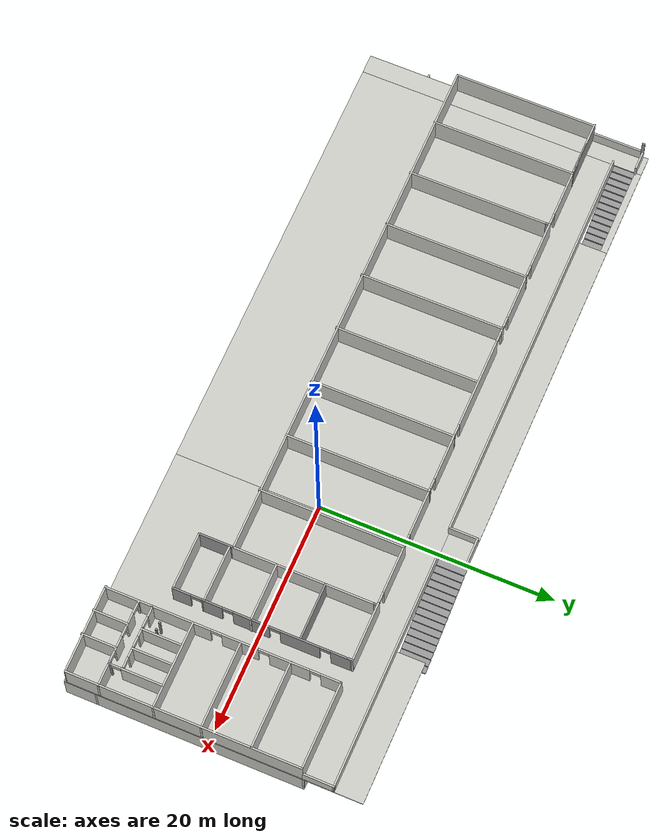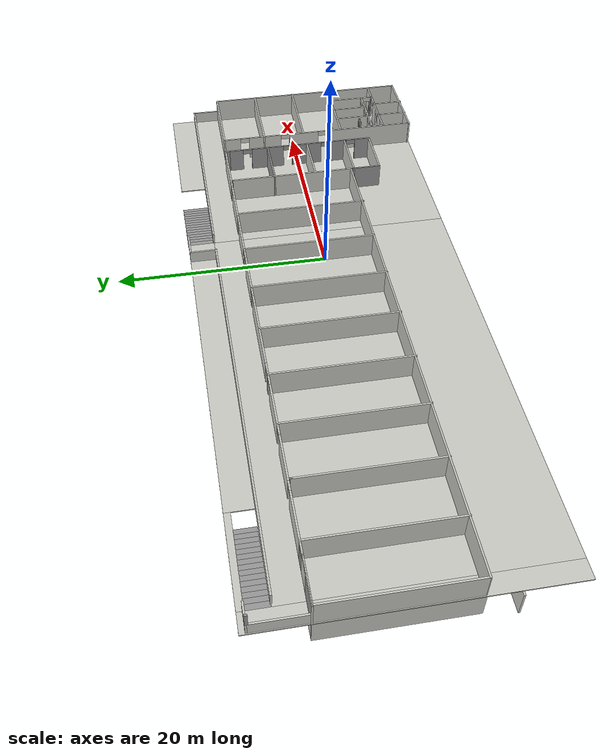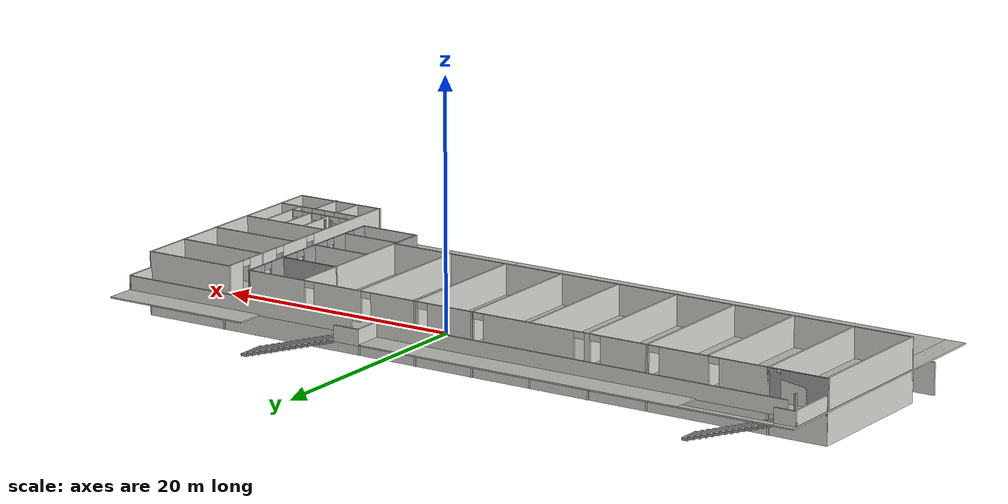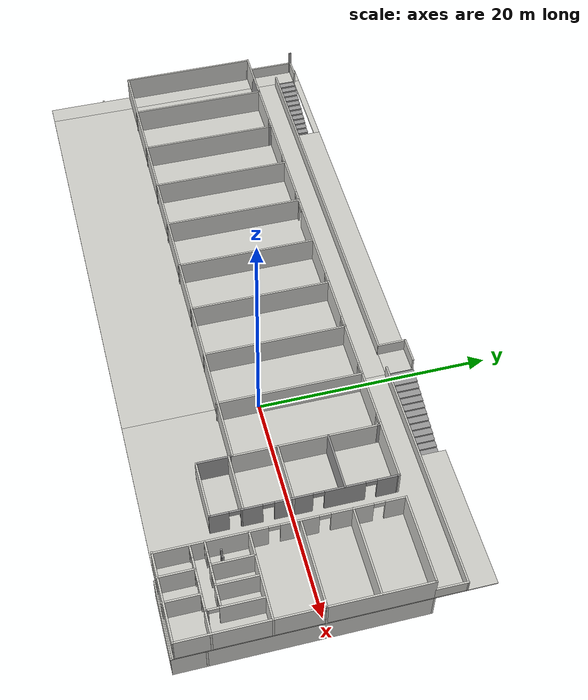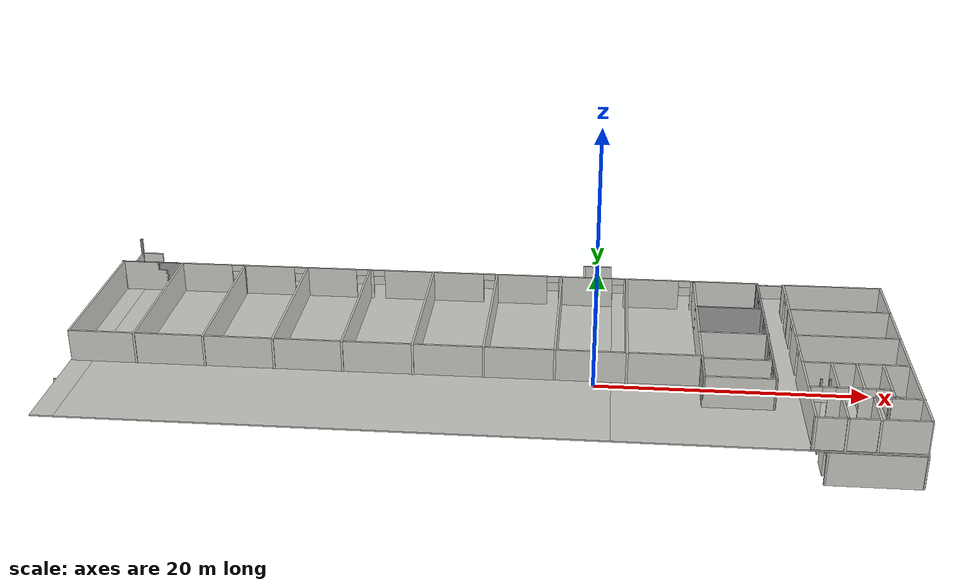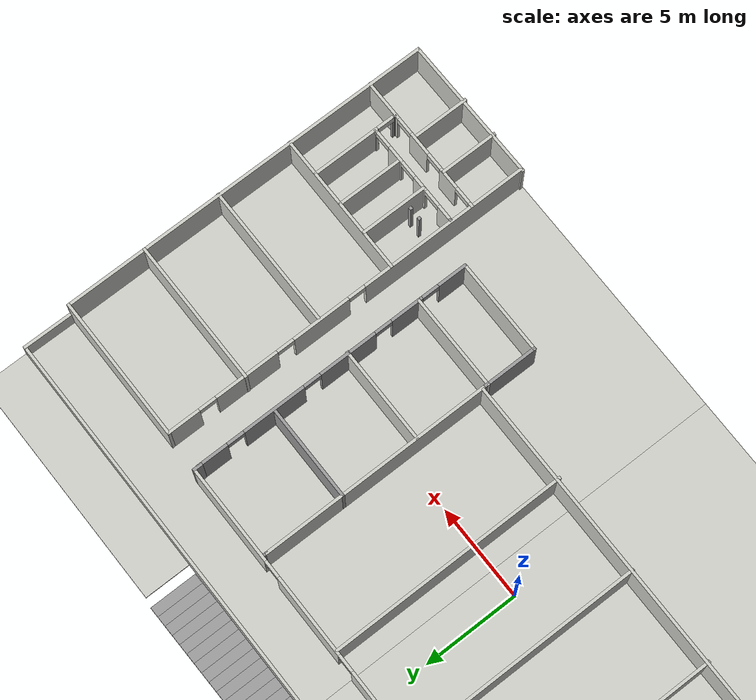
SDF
<?xml version='1.0'?>
<sdf version='1.6'>
  <model name='ifes_bloco_m'>
    <pose frame=''>-8.25935 0.618855 0 0 -0 0</pose>
    <link name='Floor_0'>
      <pose frame=''>0.157128 0.038162 2.5 0 -0 0</pose>
      <visual name='Floor_0_Visual_0'>
        <pose frame=''>-28.976 0 0.05 0 -0 0</pose>
        <geometry>
          <box>
            <size>1.64864 24.7557 0.1</size>
          </box>
        </geometry>
        <material>
          <script>
            <uri>file://media/materials/scripts/gazebo.material</uri>
            <name>Gazebo/CeilingTiled</name>
          </script>
          <ambient>1 1 1 1</ambient>
        </material>
        <meta>
          <layer>1</layer>
        </meta>
      </visual>
      <collision name='Floor_0_Collision_0'>
        <geometry>
          <box>
            <size>1.64864 24.7557 0.1</size>
          </box>
        </geometry>
        <pose frame=''>-28.976 0 0.05 0 -0 0</pose>
      </collision>
      <visual name='Floor_0_Visual_1'>
        <pose frame=''>-9.42841 -1.21298 0.05 0 -0 0</pose>
        <geometry>
          <box>
            <size>37.4466 22.3297 0.1</size>
          </box>
        </geometry>
        <material>
          <script>
            <uri>file://media/materials/scripts/gazebo.material</uri>
            <name>Gazebo/CeilingTiled</name>
          </script>
          <ambient>1 1 1 1</ambient>
        </material>
        <meta>
          <layer>1</layer>
        </meta>
      </visual>
      <collision name='Floor_0_Collision_1'>
        <geometry>
          <box>
            <size>37.4466 22.3297 0.1</size>
          </box>
        </geometry>
        <pose frame=''>-9.42841 -1.21298 0.05 0 -0 0</pose>
      </collision>
      <visual name='Floor_0_Visual_2'>
        <pose frame=''>19.5476 -1.22768 0.05 0 -0 0</pose>
        <geometry>
          <box>
            <size>20.5055 22.3003 0.1</size>
          </box>
        </geometry>
        <material>
          <script>
            <uri>file://media/materials/scripts/gazebo.material</uri>
            <name>Gazebo/CeilingTiled</name>
          </script>
          <ambient>1 1 1 1</ambient>
        </material>
        <meta>
          <layer>1</layer>
        </meta>
      </visual>
      <collision name='Floor_0_Collision_2'>
        <geometry>
          <box>
            <size>20.5055 22.3003 0.1</size>
          </box>
        </geometry>
        <pose frame=''>19.5476 -1.22768 0.05 0 -0 0</pose>
      </collision>
      <visual name='Floor_0_Visual_3'>
        <pose frame=''>23.7241 11.1502 0.05 0 -0 0</pose>
        <geometry>
          <box>
            <size>12.1525 2.45536 0.1</size>
          </box>
        </geometry>
        <material>
          <script>
            <uri>file://media/materials/scripts/gazebo.material</uri>
            <name>Gazebo/CeilingTiled</name>
          </script>
          <ambient>1 1 1 1</ambient>
        </material>
        <meta>
          <layer>1</layer>
        </meta>
      </visual>
      <collision name='Floor_0_Collision_3'>
        <geometry>
          <box>
            <size>12.1525 2.45536 0.1</size>
          </box>
        </geometry>
        <pose frame=''>23.7241 11.1502 0.05 0 -0 0</pose>
      </collision>
      <visual name='Floor_0_Visual_4'>
        <pose frame=''>-5.55039 11.1649 0.05 0 -0 0</pose>
        <geometry>
          <box>
            <size>29.6905 2.42596 0.1</size>
          </box>
        </geometry>
        <material>
          <script>
            <uri>file://media/materials/scripts/gazebo.material</uri>
            <name>Gazebo/CeilingTiled</name>
          </script>
          <ambient>1 1 1 1</ambient>
        </material>
        <meta>
          <layer>1</layer>
        </meta>
      </visual>
      <collision name='Floor_0_Collision_4'>
        <geometry>
          <box>
            <size>29.6905 2.42596 0.1</size>
          </box>
        </geometry>
        <pose frame=''>-5.55039 11.1649 0.05 0 -0 0</pose>
      </collision>
      <visual name='Floor_0_Visual_5'>
        <pose frame=''>-24.2737 12.1043 0.05 0 -0 0</pose>
        <geometry>
          <box>
            <size>7.75603 0.546998 0.1</size>
          </box>
        </geometry>
        <material>
          <script>
            <uri>file://media/materials/scripts/gazebo.material</uri>
            <name>Gazebo/CeilingTiled</name>
          </script>
          <ambient>1 1 1 1</ambient>
        </material>
        <meta>
          <layer>1</layer>
        </meta>
      </visual>
      <collision name='Floor_0_Collision_5'>
        <geometry>
          <box>
            <size>7.75603 0.546998 0.1</size>
          </box>
        </geometry>
        <pose frame=''>-24.2737 12.1043 0.05 0 -0 0</pose>
      </collision>
    </link>
    <link name='Stairs_0'>
      <visual name='Stairs_0_Visual_0'>
        <pose frame=''>-20.4971 10.9295 0.083333 0 -0 -1.5708</pose>
        <geometry>
          <box>
            <size>1.87896 0.517069 0.166667</size>
          </box>
        </geometry>
        <material>
          <script>
            <uri>file://media/materials/scripts/gazebo.material</uri>
            <name>Gazebo/Grey</name>
          </script>
          <ambient>1 1 1 1</ambient>
        </material>
        <meta>
          <layer>0</layer>
        </meta>
      </visual>
      <collision name='Stairs_0_Collision_0'>
        <geometry>
          <box>
            <size>1.87896 0.517069 0.166667</size>
          </box>
        </geometry>
        <pose frame=''>-20.4971 10.9295 0.083333 0 -0 -1.5708</pose>
      </collision>
      <visual name='Stairs_0_Visual_1'>
        <pose frame=''>-21.0141 10.9295 0.25 0 -0 -1.5708</pose>
        <geometry>
          <box>
            <size>1.87896 0.517069 0.166667</size>
          </box>
        </geometry>
        <material>
          <script>
            <uri>file://media/materials/scripts/gazebo.material</uri>
            <name>Gazebo/Grey</name>
          </script>
          <ambient>1 1 1 1</ambient>
        </material>
        <meta>
          <layer>0</layer>
        </meta>
      </visual>
      <collision name='Stairs_0_Collision_1'>
        <geometry>
          <box>
            <size>1.87896 0.517069 0.166667</size>
          </box>
        </geometry>
        <pose frame=''>-21.0141 10.9295 0.25 0 -0 -1.5708</pose>
      </collision>
      <visual name='Stairs_0_Visual_2'>
        <pose frame=''>-21.5312 10.9295 0.416667 0 -0 -1.5708</pose>
        <geometry>
          <box>
            <size>1.87896 0.517069 0.166667</size>
          </box>
        </geometry>
        <material>
          <script>
            <uri>file://media/materials/scripts/gazebo.material</uri>
            <name>Gazebo/Grey</name>
          </script>
          <ambient>1 1 1 1</ambient>
        </material>
        <meta>
          <layer>0</layer>
        </meta>
      </visual>
      <collision name='Stairs_0_Collision_2'>
        <geometry>
          <box>
            <size>1.87896 0.517069 0.166667</size>
          </box>
        </geometry>
        <pose frame=''>-21.5312 10.9295 0.416667 0 -0 -1.5708</pose>
      </collision>
      <visual name='Stairs_0_Visual_3'>
        <pose frame=''>-22.0483 10.9295 0.583333 0 -0 -1.5708</pose>
        <geometry>
          <box>
            <size>1.87896 0.517069 0.166667</size>
          </box>
        </geometry>
        <material>
          <script>
            <uri>file://media/materials/scripts/gazebo.material</uri>
            <name>Gazebo/Grey</name>
          </script>
          <ambient>1 1 1 1</ambient>
        </material>
        <meta>
          <layer>0</layer>
        </meta>
      </visual>
      <collision name='Stairs_0_Collision_3'>
        <geometry>
          <box>
            <size>1.87896 0.517069 0.166667</size>
          </box>
        </geometry>
        <pose frame=''>-22.0483 10.9295 0.583333 0 -0 -1.5708</pose>
      </collision>
      <visual name='Stairs_0_Visual_4'>
        <pose frame=''>-22.5653 10.9295 0.75 0 -0 -1.5708</pose>
        <geometry>
          <box>
            <size>1.87896 0.517069 0.166667</size>
          </box>
        </geometry>
        <material>
          <script>
            <uri>file://media/materials/scripts/gazebo.material</uri>
            <name>Gazebo/Grey</name>
          </script>
          <ambient>1 1 1 1</ambient>
        </material>
        <meta>
          <layer>0</layer>
        </meta>
      </visual>
      <collision name='Stairs_0_Collision_4'>
        <geometry>
          <box>
            <size>1.87896 0.517069 0.166667</size>
          </box>
        </geometry>
        <pose frame=''>-22.5653 10.9295 0.75 0 -0 -1.5708</pose>
      </collision>
      <visual name='Stairs_0_Visual_5'>
        <pose frame=''>-23.0824 10.9295 0.916667 0 -0 -1.5708</pose>
        <geometry>
          <box>
            <size>1.87896 0.517069 0.166667</size>
          </box>
        </geometry>
        <material>
          <script>
            <uri>file://media/materials/scripts/gazebo.material</uri>
            <name>Gazebo/Grey</name>
          </script>
          <ambient>1 1 1 1</ambient>
        </material>
        <meta>
          <layer>0</layer>
        </meta>
      </visual>
      <collision name='Stairs_0_Collision_5'>
        <geometry>
          <box>
            <size>1.87896 0.517069 0.166667</size>
          </box>
        </geometry>
        <pose frame=''>-23.0824 10.9295 0.916667 0 -0 -1.5708</pose>
      </collision>
      <visual name='Stairs_0_Visual_6'>
        <pose frame=''>-23.5995 10.9295 1.08333 0 -0 -1.5708</pose>
        <geometry>
          <box>
            <size>1.87896 0.517069 0.166667</size>
          </box>
        </geometry>
        <material>
          <script>
            <uri>file://media/materials/scripts/gazebo.material</uri>
            <name>Gazebo/Grey</name>
          </script>
          <ambient>1 1 1 1</ambient>
        </material>
        <meta>
          <layer>0</layer>
        </meta>
      </visual>
      <collision name='Stairs_0_Collision_6'>
        <geometry>
          <box>
            <size>1.87896 0.517069 0.166667</size>
          </box>
        </geometry>
        <pose frame=''>-23.5995 10.9295 1.08333 0 -0 -1.5708</pose>
      </collision>
      <visual name='Stairs_0_Visual_7'>
        <pose frame=''>-24.1166 10.9295 1.25 0 -0 -1.5708</pose>
        <geometry>
          <box>
            <size>1.87896 0.517069 0.166667</size>
          </box>
        </geometry>
        <material>
          <script>
            <uri>file://media/materials/scripts/gazebo.material</uri>
            <name>Gazebo/Grey</name>
          </script>
          <ambient>1 1 1 1</ambient>
        </material>
        <meta>
          <layer>0</layer>
        </meta>
      </visual>
      <collision name='Stairs_0_Collision_7'>
        <geometry>
          <box>
            <size>1.87896 0.517069 0.166667</size>
          </box>
        </geometry>
        <pose frame=''>-24.1166 10.9295 1.25 0 -0 -1.5708</pose>
      </collision>
      <visual name='Stairs_0_Visual_8'>
        <pose frame=''>-24.6336 10.9295 1.41667 0 -0 -1.5708</pose>
        <geometry>
          <box>
            <size>1.87896 0.517069 0.166667</size>
          </box>
        </geometry>
        <material>
          <script>
            <uri>file://media/materials/scripts/gazebo.material</uri>
            <name>Gazebo/Grey</name>
          </script>
          <ambient>1 1 1 1</ambient>
        </material>
        <meta>
          <layer>0</layer>
        </meta>
      </visual>
      <collision name='Stairs_0_Collision_8'>
        <geometry>
          <box>
            <size>1.87896 0.517069 0.166667</size>
          </box>
        </geometry>
        <pose frame=''>-24.6336 10.9295 1.41667 0 -0 -1.5708</pose>
      </collision>
      <visual name='Stairs_0_Visual_9'>
        <pose frame=''>-25.1507 10.9295 1.58333 0 -0 -1.5708</pose>
        <geometry>
          <box>
            <size>1.87896 0.517069 0.166667</size>
          </box>
        </geometry>
        <material>
          <script>
            <uri>file://media/materials/scripts/gazebo.material</uri>
            <name>Gazebo/Grey</name>
          </script>
          <ambient>1 1 1 1</ambient>
        </material>
        <meta>
          <layer>0</layer>
        </meta>
      </visual>
      <collision name='Stairs_0_Collision_9'>
        <geometry>
          <box>
            <size>1.87896 0.517069 0.166667</size>
          </box>
        </geometry>
        <pose frame=''>-25.1507 10.9295 1.58333 0 -0 -1.5708</pose>
      </collision>
      <visual name='Stairs_0_Visual_10'>
        <pose frame=''>-25.6678 10.9295 1.75 0 -0 -1.5708</pose>
        <geometry>
          <box>
            <size>1.87896 0.517069 0.166667</size>
          </box>
        </geometry>
        <material>
          <script>
            <uri>file://media/materials/scripts/gazebo.material</uri>
            <name>Gazebo/Grey</name>
          </script>
          <ambient>1 1 1 1</ambient>
        </material>
        <meta>
          <layer>0</layer>
        </meta>
      </visual>
      <collision name='Stairs_0_Collision_10'>
        <geometry>
          <box>
            <size>1.87896 0.517069 0.166667</size>
          </box>
        </geometry>
        <pose frame=''>-25.6678 10.9295 1.75 0 -0 -1.5708</pose>
      </collision>
      <visual name='Stairs_0_Visual_11'>
        <pose frame=''>-26.1848 10.9295 1.91667 0 -0 -1.5708</pose>
        <geometry>
          <box>
            <size>1.87896 0.517069 0.166667</size>
          </box>
        </geometry>
        <material>
          <script>
            <uri>file://media/materials/scripts/gazebo.material</uri>
            <name>Gazebo/Grey</name>
          </script>
          <ambient>1 1 1 1</ambient>
        </material>
        <meta>
          <layer>0</layer>
        </meta>
      </visual>
      <collision name='Stairs_0_Collision_11'>
        <geometry>
          <box>
            <size>1.87896 0.517069 0.166667</size>
          </box>
        </geometry>
        <pose frame=''>-26.1848 10.9295 1.91667 0 -0 -1.5708</pose>
      </collision>
      <visual name='Stairs_0_Visual_12'>
        <pose frame=''>-26.7019 10.9295 2.08333 0 -0 -1.5708</pose>
        <geometry>
          <box>
            <size>1.87896 0.517069 0.166667</size>
          </box>
        </geometry>
        <material>
          <script>
            <uri>file://media/materials/scripts/gazebo.material</uri>
            <name>Gazebo/Grey</name>
          </script>
          <ambient>1 1 1 1</ambient>
        </material>
        <meta>
          <layer>0</layer>
        </meta>
      </visual>
      <collision name='Stairs_0_Collision_12'>
        <geometry>
          <box>
            <size>1.87896 0.517069 0.166667</size>
          </box>
        </geometry>
        <pose frame=''>-26.7019 10.9295 2.08333 0 -0 -1.5708</pose>
      </collision>
      <visual name='Stairs_0_Visual_13'>
        <pose frame=''>-27.219 10.9295 2.25 0 -0 -1.5708</pose>
        <geometry>
          <box>
            <size>1.87896 0.517069 0.166667</size>
          </box>
        </geometry>
        <material>
          <script>
            <uri>file://media/materials/scripts/gazebo.material</uri>
            <name>Gazebo/Grey</name>
          </script>
          <ambient>1 1 1 1</ambient>
        </material>
        <meta>
          <layer>0</layer>
        </meta>
      </visual>
      <collision name='Stairs_0_Collision_13'>
        <geometry>
          <box>
            <size>1.87896 0.517069 0.166667</size>
          </box>
        </geometry>
        <pose frame=''>-27.219 10.9295 2.25 0 -0 -1.5708</pose>
      </collision>
      <visual name='Stairs_0_Visual_14'>
        <pose frame=''>-27.736 10.9295 2.41667 0 -0 -1.5708</pose>
        <geometry>
          <box>
            <size>1.87896 0.517069 0.166667</size>
          </box>
        </geometry>
        <material>
          <script>
            <uri>file://media/materials/scripts/gazebo.material</uri>
            <name>Gazebo/Grey</name>
          </script>
          <ambient>1 1 1 1</ambient>
        </material>
        <meta>
          <layer>0</layer>
        </meta>
      </visual>
      <collision name='Stairs_0_Collision_14'>
        <geometry>
          <box>
            <size>1.87896 0.517069 0.166667</size>
          </box>
        </geometry>
        <pose frame=''>-27.736 10.9295 2.41667 0 -0 -1.5708</pose>
      </collision>
    </link>
    <link name='Stairs_1'>
      <visual name='Stairs_1_Visual_0'>
        <pose frame=''>17.5266 11.2024 0.083333 0 -0 -1.5708</pose>
        <geometry>
          <box>
            <size>2.4835 0.556867 0.166667</size>
          </box>
        </geometry>
        <material>
          <script>
            <uri>file://media/materials/scripts/gazebo.material</uri>
            <name>Gazebo/Grey</name>
          </script>
          <ambient>1 1 1 1</ambient>
        </material>
        <meta>
          <layer>0</layer>
        </meta>
      </visual>
      <collision name='Stairs_1_Collision_0'>
        <geometry>
          <box>
            <size>2.4835 0.556867 0.166667</size>
          </box>
        </geometry>
        <pose frame=''>17.5266 11.2024 0.083333 0 -0 -1.5708</pose>
      </collision>
      <visual name='Stairs_1_Visual_1'>
        <pose frame=''>16.9697 11.2024 0.25 0 -0 -1.5708</pose>
        <geometry>
          <box>
            <size>2.4835 0.556867 0.166667</size>
          </box>
        </geometry>
        <material>
          <script>
            <uri>file://media/materials/scripts/gazebo.material</uri>
            <name>Gazebo/Grey</name>
          </script>
          <ambient>1 1 1 1</ambient>
        </material>
        <meta>
          <layer>0</layer>
        </meta>
      </visual>
      <collision name='Stairs_1_Collision_1'>
        <geometry>
          <box>
            <size>2.4835 0.556867 0.166667</size>
          </box>
        </geometry>
        <pose frame=''>16.9697 11.2024 0.25 0 -0 -1.5708</pose>
      </collision>
      <visual name='Stairs_1_Visual_2'>
        <pose frame=''>16.4128 11.2024 0.416667 0 -0 -1.5708</pose>
        <geometry>
          <box>
            <size>2.4835 0.556867 0.166667</size>
          </box>
        </geometry>
        <material>
          <script>
            <uri>file://media/materials/scripts/gazebo.material</uri>
            <name>Gazebo/Grey</name>
          </script>
          <ambient>1 1 1 1</ambient>
        </material>
        <meta>
          <layer>0</layer>
        </meta>
      </visual>
      <collision name='Stairs_1_Collision_2'>
        <geometry>
          <box>
            <size>2.4835 0.556867 0.166667</size>
          </box>
        </geometry>
        <pose frame=''>16.4128 11.2024 0.416667 0 -0 -1.5708</pose>
      </collision>
      <visual name='Stairs_1_Visual_3'>
        <pose frame=''>15.856 11.2024 0.583333 0 -0 -1.5708</pose>
        <geometry>
          <box>
            <size>2.4835 0.556867 0.166667</size>
          </box>
        </geometry>
        <material>
          <script>
            <uri>file://media/materials/scripts/gazebo.material</uri>
            <name>Gazebo/Grey</name>
          </script>
          <ambient>1 1 1 1</ambient>
        </material>
        <meta>
          <layer>0</layer>
        </meta>
      </visual>
      <collision name='Stairs_1_Collision_3'>
        <geometry>
          <box>
            <size>2.4835 0.556867 0.166667</size>
          </box>
        </geometry>
        <pose frame=''>15.856 11.2024 0.583333 0 -0 -1.5708</pose>
      </collision>
      <visual name='Stairs_1_Visual_4'>
        <pose frame=''>15.2991 11.2024 0.75 0 -0 -1.5708</pose>
        <geometry>
          <box>
            <size>2.4835 0.556867 0.166667</size>
          </box>
        </geometry>
        <material>
          <script>
            <uri>file://media/materials/scripts/gazebo.material</uri>
            <name>Gazebo/Grey</name>
          </script>
          <ambient>1 1 1 1</ambient>
        </material>
        <meta>
          <layer>0</layer>
        </meta>
      </visual>
      <collision name='Stairs_1_Collision_4'>
        <geometry>
          <box>
            <size>2.4835 0.556867 0.166667</size>
          </box>
        </geometry>
        <pose frame=''>15.2991 11.2024 0.75 0 -0 -1.5708</pose>
      </collision>
      <visual name='Stairs_1_Visual_5'>
        <pose frame=''>14.7422 11.2024 0.916667 0 -0 -1.5708</pose>
        <geometry>
          <box>
            <size>2.4835 0.556867 0.166667</size>
          </box>
        </geometry>
        <material>
          <script>
            <uri>file://media/materials/scripts/gazebo.material</uri>
            <name>Gazebo/Grey</name>
          </script>
          <ambient>1 1 1 1</ambient>
        </material>
        <meta>
          <layer>0</layer>
        </meta>
      </visual>
      <collision name='Stairs_1_Collision_5'>
        <geometry>
          <box>
            <size>2.4835 0.556867 0.166667</size>
          </box>
        </geometry>
        <pose frame=''>14.7422 11.2024 0.916667 0 -0 -1.5708</pose>
      </collision>
      <visual name='Stairs_1_Visual_6'>
        <pose frame=''>14.1854 11.2024 1.08333 0 -0 -1.5708</pose>
        <geometry>
          <box>
            <size>2.4835 0.556867 0.166667</size>
          </box>
        </geometry>
        <material>
          <script>
            <uri>file://media/materials/scripts/gazebo.material</uri>
            <name>Gazebo/Grey</name>
          </script>
          <ambient>1 1 1 1</ambient>
        </material>
        <meta>
          <layer>0</layer>
        </meta>
      </visual>
      <collision name='Stairs_1_Collision_6'>
        <geometry>
          <box>
            <size>2.4835 0.556867 0.166667</size>
          </box>
        </geometry>
        <pose frame=''>14.1854 11.2024 1.08333 0 -0 -1.5708</pose>
      </collision>
      <visual name='Stairs_1_Visual_7'>
        <pose frame=''>13.6285 11.2024 1.25 0 -0 -1.5708</pose>
        <geometry>
          <box>
            <size>2.4835 0.556867 0.166667</size>
          </box>
        </geometry>
        <material>
          <script>
            <uri>file://media/materials/scripts/gazebo.material</uri>
            <name>Gazebo/Grey</name>
          </script>
          <ambient>1 1 1 1</ambient>
        </material>
        <meta>
          <layer>0</layer>
        </meta>
      </visual>
      <collision name='Stairs_1_Collision_7'>
        <geometry>
          <box>
            <size>2.4835 0.556867 0.166667</size>
          </box>
        </geometry>
        <pose frame=''>13.6285 11.2024 1.25 0 -0 -1.5708</pose>
      </collision>
      <visual name='Stairs_1_Visual_8'>
        <pose frame=''>13.0716 11.2024 1.41667 0 -0 -1.5708</pose>
        <geometry>
          <box>
            <size>2.4835 0.556867 0.166667</size>
          </box>
        </geometry>
        <material>
          <script>
            <uri>file://media/materials/scripts/gazebo.material</uri>
            <name>Gazebo/Grey</name>
          </script>
          <ambient>1 1 1 1</ambient>
        </material>
        <meta>
          <layer>0</layer>
        </meta>
      </visual>
      <collision name='Stairs_1_Collision_8'>
        <geometry>
          <box>
            <size>2.4835 0.556867 0.166667</size>
          </box>
        </geometry>
        <pose frame=''>13.0716 11.2024 1.41667 0 -0 -1.5708</pose>
      </collision>
      <visual name='Stairs_1_Visual_9'>
        <pose frame=''>12.5148 11.2024 1.58333 0 -0 -1.5708</pose>
        <geometry>
          <box>
            <size>2.4835 0.556867 0.166667</size>
          </box>
        </geometry>
        <material>
          <script>
            <uri>file://media/materials/scripts/gazebo.material</uri>
            <name>Gazebo/Grey</name>
          </script>
          <ambient>1 1 1 1</ambient>
        </material>
        <meta>
          <layer>0</layer>
        </meta>
      </visual>
      <collision name='Stairs_1_Collision_9'>
        <geometry>
          <box>
            <size>2.4835 0.556867 0.166667</size>
          </box>
        </geometry>
        <pose frame=''>12.5148 11.2024 1.58333 0 -0 -1.5708</pose>
      </collision>
      <visual name='Stairs_1_Visual_10'>
        <pose frame=''>11.9579 11.2024 1.75 0 -0 -1.5708</pose>
        <geometry>
          <box>
            <size>2.4835 0.556867 0.166667</size>
          </box>
        </geometry>
        <material>
          <script>
            <uri>file://media/materials/scripts/gazebo.material</uri>
            <name>Gazebo/Grey</name>
          </script>
          <ambient>1 1 1 1</ambient>
        </material>
        <meta>
          <layer>0</layer>
        </meta>
      </visual>
      <collision name='Stairs_1_Collision_10'>
        <geometry>
          <box>
            <size>2.4835 0.556867 0.166667</size>
          </box>
        </geometry>
        <pose frame=''>11.9579 11.2024 1.75 0 -0 -1.5708</pose>
      </collision>
      <visual name='Stairs_1_Visual_11'>
        <pose frame=''>11.401 11.2024 1.91667 0 -0 -1.5708</pose>
        <geometry>
          <box>
            <size>2.4835 0.556867 0.166667</size>
          </box>
        </geometry>
        <material>
          <script>
            <uri>file://media/materials/scripts/gazebo.material</uri>
            <name>Gazebo/Grey</name>
          </script>
          <ambient>1 1 1 1</ambient>
        </material>
        <meta>
          <layer>0</layer>
        </meta>
      </visual>
      <collision name='Stairs_1_Collision_11'>
        <geometry>
          <box>
            <size>2.4835 0.556867 0.166667</size>
          </box>
        </geometry>
        <pose frame=''>11.401 11.2024 1.91667 0 -0 -1.5708</pose>
      </collision>
      <visual name='Stairs_1_Visual_12'>
        <pose frame=''>10.8442 11.2024 2.08333 0 -0 -1.5708</pose>
        <geometry>
          <box>
            <size>2.4835 0.556867 0.166667</size>
          </box>
        </geometry>
        <material>
          <script>
            <uri>file://media/materials/scripts/gazebo.material</uri>
            <name>Gazebo/Grey</name>
          </script>
          <ambient>1 1 1 1</ambient>
        </material>
        <meta>
          <layer>0</layer>
        </meta>
      </visual>
      <collision name='Stairs_1_Collision_12'>
        <geometry>
          <box>
            <size>2.4835 0.556867 0.166667</size>
          </box>
        </geometry>
        <pose frame=''>10.8442 11.2024 2.08333 0 -0 -1.5708</pose>
      </collision>
      <visual name='Stairs_1_Visual_13'>
        <pose frame=''>10.2873 11.2024 2.25 0 -0 -1.5708</pose>
        <geometry>
          <box>
            <size>2.4835 0.556867 0.166667</size>
          </box>
        </geometry>
        <material>
          <script>
            <uri>file://media/materials/scripts/gazebo.material</uri>
            <name>Gazebo/Grey</name>
          </script>
          <ambient>1 1 1 1</ambient>
        </material>
        <meta>
          <layer>0</layer>
        </meta>
      </visual>
      <collision name='Stairs_1_Collision_13'>
        <geometry>
          <box>
            <size>2.4835 0.556867 0.166667</size>
          </box>
        </geometry>
        <pose frame=''>10.2873 11.2024 2.25 0 -0 -1.5708</pose>
      </collision>
      <visual name='Stairs_1_Visual_14'>
        <pose frame=''>9.73044 11.2024 2.41667 0 -0 -1.5708</pose>
        <geometry>
          <box>
            <size>2.4835 0.556867 0.166667</size>
          </box>
        </geometry>
        <material>
          <script>
            <uri>file://media/materials/scripts/gazebo.material</uri>
            <name>Gazebo/Grey</name>
          </script>
          <ambient>1 1 1 1</ambient>
        </material>
        <meta>
          <layer>0</layer>
        </meta>
      </visual>
      <collision name='Stairs_1_Collision_14'>
        <geometry>
          <box>
            <size>2.4835 0.556867 0.166667</size>
          </box>
        </geometry>
        <pose frame=''>9.73044 11.2024 2.41667 0 -0 -1.5708</pose>
      </collision>
    </link>
    <link name='Wall_0'>
      <collision name='Wall_0_Collision'>
        <geometry>
          <box>
            <size>59.5 0.15 2.5</size>
          </box>
        </geometry>
        <pose frame=''>0 0 1.25 0 -0 0</pose>
      </collision>
      <visual name='Wall_0_Visual'>
        <pose frame=''>0 0 1.25 0 -0 0</pose>
        <geometry>
          <box>
            <size>59.5 0.15 2.5</size>
          </box>
        </geometry>
        <material>
          <script>
            <uri>file://media/materials/scripts/gazebo.material</uri>
            <name>Gazebo/CeilingTiled</name>
          </script>
          <ambient>1 1 1 1</ambient>
        </material>
        <meta>
          <layer>0</layer>
        </meta>
      </visual>
      <pose frame=''>0.181948 7.4609 0 0 -0 0</pose>
    </link>
    <link name='Wall_1'>
      <collision name='Wall_1_Collision'>
        <geometry>
          <box>
            <size>19.98 0.15 2.5</size>
          </box>
        </geometry>
        <pose frame=''>0 0 1.25 0 -0 0</pose>
      </collision>
      <visual name='Wall_1_Visual'>
        <pose frame=''>0 0 1.25 0 -0 0</pose>
        <geometry>
          <box>
            <size>19.98 0.15 2.5</size>
          </box>
        </geometry>
        <material>
          <script>
            <uri>file://media/materials/scripts/gazebo.material</uri>
            <name>Gazebo/CeilingTiled</name>
          </script>
          <ambient>1 1 1 1</ambient>
        </material>
        <meta>
          <layer>0</layer>
        </meta>
      </visual>
      <pose frame=''>29.8619 -2.4541 0 0 -0 -1.57029</pose>
    </link>
    <link name='Wall_10'>
      <collision name='Wall_10_Collision'>
        <geometry>
          <box>
            <size>6.25 0.15 2.5</size>
          </box>
        </geometry>
        <pose frame=''>0 0 1.25 0 -0 0</pose>
      </collision>
      <visual name='Wall_10_Visual'>
        <pose frame=''>0 0 1.25 0 -0 0</pose>
        <geometry>
          <box>
            <size>6.25 0.15 2.5</size>
          </box>
        </geometry>
        <material>
          <script>
            <uri>file://media/materials/scripts/gazebo.material</uri>
            <name>Gazebo/CeilingTiled</name>
          </script>
          <ambient>1 1 1 1</ambient>
        </material>
        <meta>
          <layer>0</layer>
        </meta>
      </visual>
      <pose frame=''>26.7153 -7.31464 0 0 -0 3.14159</pose>
    </link>
    <link name='Wall_101'>
      <collision name='Wall_101_Collision'>
        <geometry>
          <box>
            <size>5 0.15 2.5</size>
          </box>
        </geometry>
        <pose frame=''>0 0 1.25 0 -0 0</pose>
      </collision>
      <visual name='Wall_101_Visual'>
        <pose frame=''>0 0 1.25 0 -0 0</pose>
        <geometry>
          <box>
            <size>5 0.15 2.5</size>
          </box>
        </geometry>
        <material>
          <script>
            <uri>file://media/materials/scripts/gazebo.material</uri>
            <name>Gazebo/CeilingTiled</name>
          </script>
          <ambient>1 1 1 1</ambient>
        </material>
        <meta>
          <layer>1</layer>
        </meta>
      </visual>
      <pose frame=''>18.1581 -0.902525 2.5 0 -0 3.14159</pose>
    </link>
    <link name='Wall_104'>
      <collision name='Wall_104_Collision'>
        <geometry>
          <box>
            <size>4.54023 0.15 1.25</size>
          </box>
        </geometry>
        <pose frame=''>0 0 0.625 0 -0 0</pose>
      </collision>
      <visual name='Wall_104_Visual'>
        <pose frame=''>0 0 0.625 0 -0 0</pose>
        <geometry>
          <box>
            <size>4.54023 0.15 1.25</size>
          </box>
        </geometry>
        <material>
          <script>
            <uri>file://media/materials/scripts/gazebo.material</uri>
            <name>Gazebo/CeilingTiled</name>
          </script>
          <ambient>0.921569 0.807843 0.615686 1</ambient>
        </material>
        <meta>
          <layer>1</layer>
        </meta>
      </visual>
      <pose frame=''>-29.4926 9.61614 2.5 0 -0 1.5708</pose>
    </link>
    <link name='Wall_105'>
      <collision name='Wall_105_Collision'>
        <geometry>
          <box>
            <size>0.25 0.15 2.5</size>
          </box>
        </geometry>
        <pose frame=''>0 0 1.25 0 -0 0</pose>
      </collision>
      <visual name='Wall_105_Visual'>
        <pose frame=''>0 0 1.25 0 -0 0</pose>
        <geometry>
          <box>
            <size>0.25 0.15 2.5</size>
          </box>
        </geometry>
        <material>
          <script>
            <uri>file://media/materials/scripts/gazebo.material</uri>
            <name>Gazebo/Grey</name>
          </script>
          <ambient>1 1 1 1</ambient>
        </material>
        <meta>
          <layer>1</layer>
        </meta>
      </visual>
      <pose frame=''>-29.4926 11.8611 2.5 0 -0 1.5708</pose>
    </link>
    <link name='Wall_106'>
      <collision name='Wall_106_Collision'>
        <geometry>
          <box>
            <size>1.75 0.15 1.25</size>
          </box>
        </geometry>
        <pose frame=''>0 0 0.625 0 -0 0</pose>
      </collision>
      <visual name='Wall_106_Visual'>
        <pose frame=''>0 0 0.625 0 -0 0</pose>
        <geometry>
          <box>
            <size>1.75 0.15 1.25</size>
          </box>
        </geometry>
        <material>
          <script>
            <uri>file://media/materials/scripts/gazebo.material</uri>
            <name>Gazebo/CeilingTiled</name>
          </script>
          <ambient>0.921569 0.807843 0.615686 1</ambient>
        </material>
        <meta>
          <layer>1</layer>
        </meta>
      </visual>
      <pose frame=''>-28.6927 11.9111 2.5 0 -0 0</pose>
    </link>
    <link name='Wall_108'>
      <collision name='Wall_108_Collision'>
        <geometry>
          <box>
            <size>35 0.15 1.25</size>
          </box>
        </geometry>
        <pose frame=''>0 0 0.625 0 -0 0</pose>
      </collision>
      <visual name='Wall_108_Visual'>
        <pose frame=''>0 0 0.625 0 -0 0</pose>
        <geometry>
          <box>
            <size>35 0.15 1.25</size>
          </box>
        </geometry>
        <material>
          <script>
            <uri>file://media/materials/scripts/gazebo.material</uri>
            <name>Gazebo/CeilingTiled</name>
          </script>
          <ambient>0.921569 0.807843 0.615686 1</ambient>
        </material>
        <meta>
          <layer>1</layer>
        </meta>
      </visual>
      <pose frame=''>-10.2627 9.98214 2.5 0 -0 0</pose>
    </link>
    <link name='Wall_110'>
      <collision name='Wall_110_Collision'>
        <geometry>
          <box>
            <size>2.5 0.15 1.25</size>
          </box>
        </geometry>
        <pose frame=''>0 0 0.625 0 -0 0</pose>
      </collision>
      <visual name='Wall_110_Visual'>
        <pose frame=''>0 0 0.625 0 -0 0</pose>
        <geometry>
          <box>
            <size>2.5 0.15 1.25</size>
          </box>
        </geometry>
        <material>
          <script>
            <uri>file://media/materials/scripts/gazebo.material</uri>
            <name>Gazebo/CeilingTiled</name>
          </script>
          <ambient>0.921569 0.807843 0.615686 1</ambient>
        </material>
        <meta>
          <layer>1</layer>
        </meta>
      </visual>
      <pose frame=''>7.19935 11.1661 2.5 0 -0 1.5708</pose>
    </link>
    <link name='Wall_111'>
      <collision name='Wall_111_Collision'>
        <geometry>
          <box>
            <size>2.25 0.15 1.25</size>
          </box>
        </geometry>
        <pose frame=''>0 0 0.625 0 -0 0</pose>
      </collision>
      <visual name='Wall_111_Visual'>
        <pose frame=''>0 0 0.625 0 -0 0</pose>
        <geometry>
          <box>
            <size>2.25 0.15 1.25</size>
          </box>
        </geometry>
        <material>
          <script>
            <uri>file://media/materials/scripts/gazebo.material</uri>
            <name>Gazebo/CeilingTiled</name>
          </script>
          <ambient>0.921569 0.807843 0.615686 1</ambient>
        </material>
        <meta>
          <layer>1</layer>
        </meta>
      </visual>
      <pose frame=''>8.24935 12.3411 2.5 0 -0 0</pose>
    </link>
    <link name='Wall_115'>
      <collision name='Wall_115_Collision'>
        <geometry>
          <box>
            <size>20.5 0.15 1.2</size>
          </box>
        </geometry>
        <pose frame=''>0 0 0.6 0 -0 0</pose>
      </collision>
      <visual name='Wall_115_Visual'>
        <pose frame=''>0 0 0.6 0 -0 0</pose>
        <geometry>
          <box>
            <size>20.5 0.15 1.2</size>
          </box>
        </geometry>
        <material>
          <script>
            <uri>file://media/materials/scripts/gazebo.material</uri>
            <name>Gazebo/CeilingTiled</name>
          </script>
          <ambient>0.921569 0.807843 0.615686 1</ambient>
        </material>
        <meta>
          <layer>1</layer>
        </meta>
      </visual>
      <pose frame=''>19.7014 9.98264 2.5 0 -0 -0.000737</pose>
    </link>
    <link name='Wall_118'>
      <collision name='Wall_118_Collision'>
        <geometry>
          <box>
            <size>7.5 0.15 2.5</size>
          </box>
        </geometry>
        <pose frame=''>0 0 1.25 0 -0 0</pose>
      </collision>
      <visual name='Wall_118_Visual'>
        <pose frame=''>0 0 1.25 0 -0 0</pose>
        <geometry>
          <box>
            <size>7.5 0.15 2.5</size>
          </box>
        </geometry>
        <material>
          <script>
            <uri>file://media/materials/scripts/gazebo.material</uri>
            <name>Gazebo/CeilingTiled</name>
          </script>
          <ambient>1 1 1 1</ambient>
        </material>
        <meta>
          <layer>1</layer>
        </meta>
      </visual>
      <pose frame=''>26.1723 3.25797 2.5 0 -0 0</pose>
    </link>
    <link name='Wall_12'>
      <collision name='Wall_12_Collision'>
        <geometry>
          <box>
            <size>0.15 0.15 2.5</size>
          </box>
        </geometry>
        <pose frame=''>0 0 1.25 0 -0 0</pose>
      </collision>
      <visual name='Wall_12_Visual'>
        <pose frame=''>0 0 1.25 0 -0 0</pose>
        <geometry>
          <box>
            <size>0.15 0.15 2.5</size>
          </box>
        </geometry>
        <material>
          <script>
            <uri>file://media/materials/scripts/gazebo.material</uri>
            <name>Gazebo/Grey</name>
          </script>
          <ambient>1 1 1 1</ambient>
        </material>
        <meta>
          <layer>0</layer>
        </meta>
      </visual>
      <pose frame=''>23.6653 -7.31464 0 0 -0 0</pose>
    </link>
    <link name='Wall_120'>
      <collision name='Wall_120_Collision'>
        <geometry>
          <box>
            <size>7.5 0.15 2.5</size>
          </box>
        </geometry>
        <pose frame=''>0 0 1.25 0 -0 0</pose>
      </collision>
      <visual name='Wall_120_Visual'>
        <pose frame=''>0 0 1.25 0 -0 0</pose>
        <geometry>
          <box>
            <size>7.5 0.15 2.5</size>
          </box>
        </geometry>
        <material>
          <script>
            <uri>file://media/materials/scripts/gazebo.material</uri>
            <name>Gazebo/CeilingTiled</name>
          </script>
          <ambient>1 1 1 1</ambient>
        </material>
        <meta>
          <layer>1</layer>
        </meta>
      </visual>
      <pose frame=''>26.2075 -0.857943 2.5 0 -0 0</pose>
    </link>
    <link name='Wall_121'>
      <collision name='Wall_121_Collision'>
        <geometry>
          <box>
            <size>0.15 0.15 2.5</size>
          </box>
        </geometry>
        <pose frame=''>0 0 1.25 0 -0 0</pose>
      </collision>
      <visual name='Wall_121_Visual'>
        <pose frame=''>0 0 1.25 0 -0 0</pose>
        <geometry>
          <box>
            <size>0.15 0.15 2.5</size>
          </box>
        </geometry>
        <material>
          <script>
            <uri>file://media/materials/scripts/gazebo.material</uri>
            <name>Gazebo/Grey</name>
          </script>
          <ambient>1 1 1 1</ambient>
        </material>
        <meta>
          <layer>1</layer>
        </meta>
      </visual>
      <pose frame=''>29.8825 -0.857943 2.5 0 -0 0</pose>
    </link>
    <link name='Wall_124'>
      <collision name='Wall_124_Collision'>
        <geometry>
          <box>
            <size>7.5 0.15 2.5</size>
          </box>
        </geometry>
        <pose frame=''>0 0 1.25 0 -0 0</pose>
      </collision>
      <visual name='Wall_124_Visual'>
        <pose frame=''>0 0 1.25 0 -0 0</pose>
        <geometry>
          <box>
            <size>7.5 0.15 2.5</size>
          </box>
        </geometry>
        <material>
          <script>
            <uri>file://media/materials/scripts/gazebo.material</uri>
            <name>Gazebo/CeilingTiled</name>
          </script>
          <ambient>1 1 1 1</ambient>
        </material>
        <meta>
          <layer>1</layer>
        </meta>
      </visual>
      <pose frame=''>26.2012 -4.84441 2.5 0 -0 0</pose>
    </link>
    <link name='Wall_129'>
      <collision name='Wall_129_Collision'>
        <geometry>
          <box>
            <size>3.5 0.15 2.5</size>
          </box>
        </geometry>
        <pose frame=''>0 0 1.25 0 -0 0</pose>
      </collision>
      <visual name='Wall_129_Visual'>
        <pose frame=''>0 0 1.25 0 -0 0</pose>
        <geometry>
          <box>
            <size>3.5 0.15 2.5</size>
          </box>
        </geometry>
        <material>
          <script>
            <uri>file://media/materials/scripts/gazebo.material</uri>
            <name>Gazebo/CeilingTiled</name>
          </script>
          <ambient>1 1 1 1</ambient>
        </material>
        <meta>
          <layer>1</layer>
        </meta>
      </visual>
      <pose frame=''>24.5069 -6.54663 2.5 0 -0 -1.5708</pose>
    </link>
    <link name='Wall_131'>
      <collision name='Wall_131_Collision'>
        <geometry>
          <box>
            <size>3.5 0.15 2.5</size>
          </box>
        </geometry>
        <pose frame=''>0 0 1.25 0 -0 0</pose>
      </collision>
      <visual name='Wall_131_Visual'>
        <pose frame=''>0 0 1.25 0 -0 0</pose>
        <geometry>
          <box>
            <size>3.5 0.15 2.5</size>
          </box>
        </geometry>
        <material>
          <script>
            <uri>file://media/materials/scripts/gazebo.material</uri>
            <name>Gazebo/CeilingTiled</name>
          </script>
          <ambient>1 1 1 1</ambient>
        </material>
        <meta>
          <layer>1</layer>
        </meta>
      </visual>
      <pose frame=''>26.203 -6.54862 2.5 0 -0 -1.5708</pose>
    </link>
    <link name='Wall_133'>
      <pose frame=''>28.0029 -7.04663 2.5 0 -0 -1.5708</pose>
      <visual name='Wall_133_Visual_0'>
        <pose frame=''>-0.471414 0 1.25 0 -0 0</pose>
        <geometry>
          <box>
            <size>3.55717 0.15 2.5</size>
          </box>
        </geometry>
        <material>
          <script>
            <uri>file://media/materials/scripts/gazebo.material</uri>
            <name>Gazebo/CeilingTiled</name>
          </script>
          <ambient>1 1 1 1</ambient>
        </material>
        <meta>
          <layer>1</layer>
        </meta>
      </visual>
      <collision name='Wall_133_Collision_0'>
        <geometry>
          <box>
            <size>3.55717 0.15 2.5</size>
          </box>
        </geometry>
        <pose frame=''>-0.471414 0 1.25 0 -0 0</pose>
      </collision>
      <visual name='Wall_133_Visual_1'>
        <pose frame=''>2.22859 0 1.25 0 -0 0</pose>
        <geometry>
          <box>
            <size>0.042828 0.15 2.5</size>
          </box>
        </geometry>
        <material>
          <script>
            <uri>file://media/materials/scripts/gazebo.material</uri>
            <name>Gazebo/CeilingTiled</name>
          </script>
          <ambient>1 1 1 1</ambient>
        </material>
        <meta>
          <layer>1</layer>
        </meta>
      </visual>
      <collision name='Wall_133_Collision_1'>
        <geometry>
          <box>
            <size>0.042828 0.15 2.5</size>
          </box>
        </geometry>
        <pose frame=''>2.22859 0 1.25 0 -0 0</pose>
      </collision>
      <visual name='Wall_133_Visual_2'>
        <pose frame=''>1.75717 0 2.25 0 -0 0</pose>
        <geometry>
          <box>
            <size>0.9 0.15 0.5</size>
          </box>
        </geometry>
        <material>
          <script>
            <uri>file://media/materials/scripts/gazebo.material</uri>
            <name>Gazebo/CeilingTiled</name>
          </script>
          <ambient>1 1 1 1</ambient>
        </material>
        <meta>
          <layer>1</layer>
        </meta>
      </visual>
      <collision name='Wall_133_Collision_2'>
        <geometry>
          <box>
            <size>0.9 0.15 0.5</size>
          </box>
        </geometry>
        <pose frame=''>1.75717 0 2.25 0 -0 0</pose>
      </collision>
    </link>
    <link name='Wall_134'>
      <collision name='Wall_134_Collision'>
        <geometry>
          <box>
            <size>0.25 0.15 2.5</size>
          </box>
        </geometry>
        <pose frame=''>0 0 1.25 0 -0 0</pose>
      </collision>
      <visual name='Wall_134_Visual'>
        <pose frame=''>0 0 1.25 0 -0 0</pose>
        <geometry>
          <box>
            <size>0.25 0.15 2.5</size>
          </box>
        </geometry>
        <material>
          <script>
            <uri>file://media/materials/scripts/gazebo.material</uri>
            <name>Gazebo/Grey</name>
          </script>
          <ambient>1 1 1 1</ambient>
        </material>
        <meta>
          <layer>1</layer>
        </meta>
      </visual>
      <pose frame=''>28.0029 -9.27163 2.5 0 -0 -1.5708</pose>
    </link>
    <link name='Wall_136'>
      <collision name='Wall_136_Collision'>
        <geometry>
          <box>
            <size>3 0.15 2.5</size>
          </box>
        </geometry>
        <pose frame=''>0 0 1.25 0 -0 0</pose>
      </collision>
      <visual name='Wall_136_Visual'>
        <pose frame=''>0 0 1.25 0 -0 0</pose>
        <geometry>
          <box>
            <size>3 0.15 2.5</size>
          </box>
        </geometry>
        <material>
          <script>
            <uri>file://media/materials/scripts/gazebo.material</uri>
            <name>Gazebo/CeilingTiled</name>
          </script>
          <ambient>1 1 1 1</ambient>
        </material>
        <meta>
          <layer>1</layer>
        </meta>
      </visual>
      <pose frame=''>24.5584 -10.8398 2.5 0 -0 -1.5708</pose>
    </link>
    <link name='Wall_138'>
      <collision name='Wall_138_Collision'>
        <geometry>
          <box>
            <size>3 0.15 2.5</size>
          </box>
        </geometry>
        <pose frame=''>0 0 1.25 0 -0 0</pose>
      </collision>
      <visual name='Wall_138_Visual'>
        <pose frame=''>0 0 1.25 0 -0 0</pose>
        <geometry>
          <box>
            <size>3 0.15 2.5</size>
          </box>
        </geometry>
        <material>
          <script>
            <uri>file://media/materials/scripts/gazebo.material</uri>
            <name>Gazebo/CeilingTiled</name>
          </script>
          <ambient>1 1 1 1</ambient>
        </material>
        <meta>
          <layer>1</layer>
        </meta>
      </visual>
      <pose frame=''>26.6381 -10.8335 2.5 0 -0 -1.5708</pose>
    </link>
    <link name='Wall_14'>
      <collision name='Wall_14_Collision'>
        <geometry>
          <box>
            <size>6.5 0.15 2.5</size>
          </box>
        </geometry>
        <pose frame=''>0 0 1.25 0 -0 0</pose>
      </collision>
      <visual name='Wall_14_Visual'>
        <pose frame=''>0 0 1.25 0 -0 0</pose>
        <geometry>
          <box>
            <size>6.5 0.15 2.5</size>
          </box>
        </geometry>
        <material>
          <script>
            <uri>file://media/materials/scripts/gazebo.material</uri>
            <name>Gazebo/CeilingTiled</name>
          </script>
          <ambient>1 1 1 1</ambient>
        </material>
        <meta>
          <layer>0</layer>
        </meta>
      </visual>
      <pose frame=''>26.6942 -9.78365 0 0 -0 0</pose>
    </link>
    <link name='Wall_141'>
      <collision name='Wall_141_Collision'>
        <geometry>
          <box>
            <size>2.71955 0.15 1.25</size>
          </box>
        </geometry>
        <pose frame=''>0 0 0.625 0 -0 0</pose>
      </collision>
      <visual name='Wall_141_Visual'>
        <pose frame=''>0 0 0.625 0 -0 0</pose>
        <geometry>
          <box>
            <size>2.71955 0.15 1.25</size>
          </box>
        </geometry>
        <material>
          <script>
            <uri>file://media/materials/scripts/gazebo.material</uri>
            <name>Gazebo/CeilingTiled</name>
          </script>
          <ambient>0.921569 0.807843 0.615686 1</ambient>
        </material>
        <meta>
          <layer>1</layer>
        </meta>
      </visual>
      <pose frame=''>29.8668 8.69064 2.5 0 -0 -1.57819</pose>
    </link>
    <link name='Wall_144'>
      <collision name='Wall_144_Collision'>
        <geometry>
          <box>
            <size>7.50007 0.15 2.5</size>
          </box>
        </geometry>
        <pose frame=''>0 0 1.25 0 -0 0</pose>
      </collision>
      <visual name='Wall_144_Visual'>
        <pose frame=''>0 0 1.25 0 -0 0</pose>
        <geometry>
          <box>
            <size>7.50007 0.15 2.5</size>
          </box>
        </geometry>
        <material>
          <script>
            <uri>file://media/materials/scripts/gazebo.material</uri>
            <name>Gazebo/CeilingTiled</name>
          </script>
          <ambient>1 1 1 1</ambient>
        </material>
        <meta>
          <layer>1</layer>
        </meta>
      </visual>
      <pose frame=''>26.1821 7.41341 2.5 0 -0 3.13962</pose>
    </link>
    <link name='Wall_157'>
      <collision name='Wall_157_Collision'>
        <geometry>
          <box>
            <size>5 0.15 2.5</size>
          </box>
        </geometry>
        <pose frame=''>0 0 1.25 0 -0 0</pose>
      </collision>
      <visual name='Wall_157_Visual'>
        <pose frame=''>0 0 1.25 0 -0 0</pose>
        <geometry>
          <box>
            <size>5 0.15 2.5</size>
          </box>
        </geometry>
        <material>
          <script>
            <uri>file://media/materials/scripts/gazebo.material</uri>
            <name>Gazebo/Grey</name>
          </script>
          <ambient>1 1 1 1</ambient>
        </material>
        <meta>
          <layer>1</layer>
        </meta>
      </visual>
      <pose frame=''>-27.1432 7.51797 2.5 0 -0 3.14159</pose>
    </link>
    <link name='Wall_158'>
      <pose frame=''>-4.51821 7.51797 2.5 0 -0 0</pose>
      <visual name='Wall_158_Visual_0'>
        <pose frame=''>-23.1848 0 1.25 0 -0 0</pose>
        <geometry>
          <box>
            <size>3.88049 0.15 2.5</size>
          </box>
        </geometry>
        <material>
          <script>
            <uri>file://media/materials/scripts/gazebo.material</uri>
            <name>Gazebo/CeilingTiled</name>
          </script>
          <ambient>1 1 1 1</ambient>
        </material>
        <meta>
          <layer>1</layer>
        </meta>
      </visual>
      <collision name='Wall_158_Collision_0'>
        <geometry>
          <box>
            <size>3.88049 0.15 2.5</size>
          </box>
        </geometry>
        <pose frame=''>-23.1848 0 1.25 0 -0 0</pose>
      </collision>
      <visual name='Wall_158_Visual_1'>
        <pose frame=''>-18.2616 0 1.25 0 -0 0</pose>
        <geometry>
          <box>
            <size>4.16574 0.15 2.5</size>
          </box>
        </geometry>
        <material>
          <script>
            <uri>file://media/materials/scripts/gazebo.material</uri>
            <name>Gazebo/CeilingTiled</name>
          </script>
          <ambient>1 1 1 1</ambient>
        </material>
        <meta>
          <layer>1</layer>
        </meta>
      </visual>
      <collision name='Wall_158_Collision_1'>
        <geometry>
          <box>
            <size>4.16574 0.15 2.5</size>
          </box>
        </geometry>
        <pose frame=''>-18.2616 0 1.25 0 -0 0</pose>
      </collision>
      <visual name='Wall_158_Visual_2'>
        <pose frame=''>-13.2135 0 1.25 0 -0 0</pose>
        <geometry>
          <box>
            <size>4.13056 0.15 2.5</size>
          </box>
        </geometry>
        <material>
          <script>
            <uri>file://media/materials/scripts/gazebo.material</uri>
            <name>Gazebo/CeilingTiled</name>
          </script>
          <ambient>1 1 1 1</ambient>
        </material>
        <meta>
          <layer>1</layer>
        </meta>
      </visual>
      <collision name='Wall_158_Collision_2'>
        <geometry>
          <box>
            <size>4.13056 0.15 2.5</size>
          </box>
        </geometry>
        <pose frame=''>-13.2135 0 1.25 0 -0 0</pose>
      </collision>
      <visual name='Wall_158_Visual_3'>
        <pose frame=''>-8.2181 0 1.25 0 -0 0</pose>
        <geometry>
          <box>
            <size>4.0602 0.15 2.5</size>
          </box>
        </geometry>
        <material>
          <script>
            <uri>file://media/materials/scripts/gazebo.material</uri>
            <name>Gazebo/CeilingTiled</name>
          </script>
          <ambient>1 1 1 1</ambient>
        </material>
        <meta>
          <layer>1</layer>
        </meta>
      </visual>
      <collision name='Wall_158_Collision_3'>
        <geometry>
          <box>
            <size>4.0602 0.15 2.5</size>
          </box>
        </geometry>
        <pose frame=''>-8.2181 0 1.25 0 -0 0</pose>
      </collision>
      <visual name='Wall_158_Visual_4'>
        <pose frame=''>-5.05201 0 1.25 0 -0 0</pose>
        <geometry>
          <box>
            <size>0.471971 0.15 2.5</size>
          </box>
        </geometry>
        <material>
          <script>
            <uri>file://media/materials/scripts/gazebo.material</uri>
            <name>Gazebo/CeilingTiled</name>
          </script>
          <ambient>1 1 1 1</ambient>
        </material>
        <meta>
          <layer>1</layer>
        </meta>
      </visual>
      <collision name='Wall_158_Collision_4'>
        <geometry>
          <box>
            <size>0.471971 0.15 2.5</size>
          </box>
        </geometry>
        <pose frame=''>-5.05201 0 1.25 0 -0 0</pose>
      </collision>
      <visual name='Wall_158_Visual_5'>
        <pose frame=''>-0.003861 0 1.25 0 -0 0</pose>
        <geometry>
          <box>
            <size>7.82433 0.15 2.5</size>
          </box>
        </geometry>
        <material>
          <script>
            <uri>file://media/materials/scripts/gazebo.material</uri>
            <name>Gazebo/CeilingTiled</name>
          </script>
          <ambient>1 1 1 1</ambient>
        </material>
        <meta>
          <layer>1</layer>
        </meta>
      </visual>
      <collision name='Wall_158_Collision_5'>
        <geometry>
          <box>
            <size>7.82433 0.15 2.5</size>
          </box>
        </geometry>
        <pose frame=''>-0.003861 0 1.25 0 -0 0</pose>
      </collision>
      <visual name='Wall_158_Visual_6'>
        <pose frame=''>6.83841 0 1.25 0 -0 0</pose>
        <geometry>
          <box>
            <size>4.0602 0.15 2.5</size>
          </box>
        </geometry>
        <material>
          <script>
            <uri>file://media/materials/scripts/gazebo.material</uri>
            <name>Gazebo/CeilingTiled</name>
          </script>
          <ambient>1 1 1 1</ambient>
        </material>
        <meta>
          <layer>1</layer>
        </meta>
      </visual>
      <collision name='Wall_158_Collision_6'>
        <geometry>
          <box>
            <size>4.0602 0.15 2.5</size>
          </box>
        </geometry>
        <pose frame=''>6.83841 0 1.25 0 -0 0</pose>
      </collision>
      <visual name='Wall_158_Visual_7'>
        <pose frame=''>11.8514 0 1.25 0 -0 0</pose>
        <geometry>
          <box>
            <size>4.16574 0.15 2.5</size>
          </box>
        </geometry>
        <material>
          <script>
            <uri>file://media/materials/scripts/gazebo.material</uri>
            <name>Gazebo/CeilingTiled</name>
          </script>
          <ambient>1 1 1 1</ambient>
        </material>
        <meta>
          <layer>1</layer>
        </meta>
      </visual>
      <collision name='Wall_158_Collision_7'>
        <geometry>
          <box>
            <size>4.16574 0.15 2.5</size>
          </box>
        </geometry>
        <pose frame=''>11.8514 0 1.25 0 -0 0</pose>
      </collision>
      <visual name='Wall_158_Visual_8'>
        <pose frame=''>16.9523 0 1.25 0 -0 0</pose>
        <geometry>
          <box>
            <size>4.2361 0.15 2.5</size>
          </box>
        </geometry>
        <material>
          <script>
            <uri>file://media/materials/scripts/gazebo.material</uri>
            <name>Gazebo/CeilingTiled</name>
          </script>
          <ambient>1 1 1 1</ambient>
        </material>
        <meta>
          <layer>1</layer>
        </meta>
      </visual>
      <collision name='Wall_158_Collision_8'>
        <geometry>
          <box>
            <size>4.2361 0.15 2.5</size>
          </box>
        </geometry>
        <pose frame=''>16.9523 0 1.25 0 -0 0</pose>
      </collision>
      <visual name='Wall_158_Visual_9'>
        <pose frame=''>22.5477 0 1.25 0 -0 0</pose>
        <geometry>
          <box>
            <size>5.15465 0.15 2.5</size>
          </box>
        </geometry>
        <material>
          <script>
            <uri>file://media/materials/scripts/gazebo.material</uri>
            <name>Gazebo/CeilingTiled</name>
          </script>
          <ambient>1 1 1 1</ambient>
        </material>
        <meta>
          <layer>1</layer>
        </meta>
      </visual>
      <collision name='Wall_158_Collision_9'>
        <geometry>
          <box>
            <size>5.15465 0.15 2.5</size>
          </box>
        </geometry>
        <pose frame=''>22.5477 0 1.25 0 -0 0</pose>
      </collision>
      <visual name='Wall_158_Visual_10'>
        <pose frame=''>-20.7945 0 2.25 0 -0 0</pose>
        <geometry>
          <box>
            <size>0.9 0.15 0.5</size>
          </box>
        </geometry>
        <material>
          <script>
            <uri>file://media/materials/scripts/gazebo.material</uri>
            <name>Gazebo/CeilingTiled</name>
          </script>
          <ambient>1 1 1 1</ambient>
        </material>
        <meta>
          <layer>1</layer>
        </meta>
      </visual>
      <collision name='Wall_158_Collision_10'>
        <geometry>
          <box>
            <size>0.9 0.15 0.5</size>
          </box>
        </geometry>
        <pose frame=''>-20.7945 0 2.25 0 -0 0</pose>
      </collision>
      <visual name='Wall_158_Visual_11'>
        <pose frame=''>-15.7288 0 2.25 0 -0 0</pose>
        <geometry>
          <box>
            <size>0.9 0.15 0.5</size>
          </box>
        </geometry>
        <material>
          <script>
            <uri>file://media/materials/scripts/gazebo.material</uri>
            <name>Gazebo/CeilingTiled</name>
          </script>
          <ambient>1 1 1 1</ambient>
        </material>
        <meta>
          <layer>1</layer>
        </meta>
      </visual>
      <collision name='Wall_158_Collision_11'>
        <geometry>
          <box>
            <size>0.9 0.15 0.5</size>
          </box>
        </geometry>
        <pose frame=''>-15.7288 0 2.25 0 -0 0</pose>
      </collision>
      <visual name='Wall_158_Visual_12'>
        <pose frame=''>-10.6982 0 2.25 0 -0 0</pose>
        <geometry>
          <box>
            <size>0.9 0.15 0.5</size>
          </box>
        </geometry>
        <material>
          <script>
            <uri>file://media/materials/scripts/gazebo.material</uri>
            <name>Gazebo/CeilingTiled</name>
          </script>
          <ambient>1 1 1 1</ambient>
        </material>
        <meta>
          <layer>1</layer>
        </meta>
      </visual>
      <collision name='Wall_158_Collision_12'>
        <geometry>
          <box>
            <size>0.9 0.15 0.5</size>
          </box>
        </geometry>
        <pose frame=''>-10.6982 0 2.25 0 -0 0</pose>
      </collision>
      <visual name='Wall_158_Visual_13'>
        <pose frame=''>-5.738 0 2.25 0 -0 0</pose>
        <geometry>
          <box>
            <size>0.9 0.15 0.5</size>
          </box>
        </geometry>
        <material>
          <script>
            <uri>file://media/materials/scripts/gazebo.material</uri>
            <name>Gazebo/CeilingTiled</name>
          </script>
          <ambient>1 1 1 1</ambient>
        </material>
        <meta>
          <layer>1</layer>
        </meta>
      </visual>
      <collision name='Wall_158_Collision_13'>
        <geometry>
          <box>
            <size>0.9 0.15 0.5</size>
          </box>
        </geometry>
        <pose frame=''>-5.738 0 2.25 0 -0 0</pose>
      </collision>
      <visual name='Wall_158_Visual_14'>
        <pose frame=''>-4.36603 0 2.25 0 -0 0</pose>
        <geometry>
          <box>
            <size>0.9 0.15 0.5</size>
          </box>
        </geometry>
        <material>
          <script>
            <uri>file://media/materials/scripts/gazebo.material</uri>
            <name>Gazebo/CeilingTiled</name>
          </script>
          <ambient>1 1 1 1</ambient>
        </material>
        <meta>
          <layer>1</layer>
        </meta>
      </visual>
      <collision name='Wall_158_Collision_14'>
        <geometry>
          <box>
            <size>0.9 0.15 0.5</size>
          </box>
        </geometry>
        <pose frame=''>-4.36603 0 2.25 0 -0 0</pose>
      </collision>
      <visual name='Wall_158_Visual_15'>
        <pose frame=''>4.35831 0 2.25 0 -0 0</pose>
        <geometry>
          <box>
            <size>0.9 0.15 0.5</size>
          </box>
        </geometry>
        <material>
          <script>
            <uri>file://media/materials/scripts/gazebo.material</uri>
            <name>Gazebo/CeilingTiled</name>
          </script>
          <ambient>1 1 1 1</ambient>
        </material>
        <meta>
          <layer>1</layer>
        </meta>
      </visual>
      <collision name='Wall_158_Collision_15'>
        <geometry>
          <box>
            <size>0.9 0.15 0.5</size>
          </box>
        </geometry>
        <pose frame=''>4.35831 0 2.25 0 -0 0</pose>
      </collision>
      <visual name='Wall_158_Visual_16'>
        <pose frame=''>9.31851 0 2.25 0 -0 0</pose>
        <geometry>
          <box>
            <size>0.9 0.15 0.5</size>
          </box>
        </geometry>
        <material>
          <script>
            <uri>file://media/materials/scripts/gazebo.material</uri>
            <name>Gazebo/CeilingTiled</name>
          </script>
          <ambient>1 1 1 1</ambient>
        </material>
        <meta>
          <layer>1</layer>
        </meta>
      </visual>
      <collision name='Wall_158_Collision_16'>
        <geometry>
          <box>
            <size>0.9 0.15 0.5</size>
          </box>
        </geometry>
        <pose frame=''>9.31851 0 2.25 0 -0 0</pose>
      </collision>
      <visual name='Wall_158_Visual_17'>
        <pose frame=''>14.3843 0 2.25 0 -0 0</pose>
        <geometry>
          <box>
            <size>0.9 0.15 0.5</size>
          </box>
        </geometry>
        <material>
          <script>
            <uri>file://media/materials/scripts/gazebo.material</uri>
            <name>Gazebo/CeilingTiled</name>
          </script>
          <ambient>1 1 1 1</ambient>
        </material>
        <meta>
          <layer>1</layer>
        </meta>
      </visual>
      <collision name='Wall_158_Collision_17'>
        <geometry>
          <box>
            <size>0.9 0.15 0.5</size>
          </box>
        </geometry>
        <pose frame=''>14.3843 0 2.25 0 -0 0</pose>
      </collision>
      <visual name='Wall_158_Visual_18'>
        <pose frame=''>19.5204 0 2.25 0 -0 0</pose>
        <geometry>
          <box>
            <size>0.9 0.15 0.5</size>
          </box>
        </geometry>
        <material>
          <script>
            <uri>file://media/materials/scripts/gazebo.material</uri>
            <name>Gazebo/CeilingTiled</name>
          </script>
          <ambient>1 1 1 1</ambient>
        </material>
        <meta>
          <layer>1</layer>
        </meta>
      </visual>
      <collision name='Wall_158_Collision_18'>
        <geometry>
          <box>
            <size>0.9 0.15 0.5</size>
          </box>
        </geometry>
        <pose frame=''>19.5204 0 2.25 0 -0 0</pose>
      </collision>
    </link>
    <link name='Wall_159'>
      <collision name='Wall_159_Collision'>
        <geometry>
          <box>
            <size>0.5 0.15 2.5</size>
          </box>
        </geometry>
        <pose frame=''>0 0 1.25 0 -0 0</pose>
      </collision>
      <visual name='Wall_159_Visual'>
        <pose frame=''>0 0 1.25 0 -0 0</pose>
        <geometry>
          <box>
            <size>0.5 0.15 2.5</size>
          </box>
        </geometry>
        <material>
          <script>
            <uri>file://media/materials/scripts/gazebo.material</uri>
            <name>Gazebo/Grey</name>
          </script>
          <ambient>1 1 1 1</ambient>
        </material>
        <meta>
          <layer>1</layer>
        </meta>
      </visual>
      <pose frame=''>20.5318 7.34297 2.5 0 -0 -1.5708</pose>
    </link>
    <link name='Wall_16'>
      <collision name='Wall_16_Collision'>
        <geometry>
          <box>
            <size>0.508751 0.15 2.5</size>
          </box>
        </geometry>
        <pose frame=''>0 0 1.25 0 -0 0</pose>
      </collision>
      <visual name='Wall_16_Visual'>
        <pose frame=''>0 0 1.25 0 -0 0</pose>
        <geometry>
          <box>
            <size>0.508751 0.15 2.5</size>
          </box>
        </geometry>
        <material>
          <script>
            <uri>file://media/materials/scripts/gazebo.material</uri>
            <name>Gazebo/Grey</name>
          </script>
          <ambient>1 1 1 1</ambient>
        </material>
        <meta>
          <layer>0</layer>
        </meta>
      </visual>
      <pose frame=''>23.5113 -7.36843 0 0 -0 1.5949</pose>
    </link>
    <link name='Wall_17'>
      <collision name='Wall_17_Collision'>
        <geometry>
          <box>
            <size>0.15 0.15 2.5</size>
          </box>
        </geometry>
        <pose frame=''>0 0 1.25 0 -0 0</pose>
      </collision>
      <visual name='Wall_17_Visual'>
        <pose frame=''>0 0 1.25 0 -0 0</pose>
        <geometry>
          <box>
            <size>0.15 0.15 2.5</size>
          </box>
        </geometry>
        <material>
          <script>
            <uri>file://media/materials/scripts/gazebo.material</uri>
            <name>Gazebo/Grey</name>
          </script>
          <ambient>1 1 1 1</ambient>
        </material>
        <meta>
          <layer>0</layer>
        </meta>
      </visual>
      <pose frame=''>23.5069 -7.1891 0 0 -0 0</pose>
    </link>
    <link name='Wall_18'>
      <collision name='Wall_18_Collision'>
        <geometry>
          <box>
            <size>0.75 0.15 2.5</size>
          </box>
        </geometry>
        <pose frame=''>0 0 1.25 0 -0 0</pose>
      </collision>
      <visual name='Wall_18_Visual'>
        <pose frame=''>0 0 1.25 0 -0 0</pose>
        <geometry>
          <box>
            <size>0.75 0.15 2.5</size>
          </box>
        </geometry>
        <material>
          <script>
            <uri>file://media/materials/scripts/gazebo.material</uri>
            <name>Gazebo/CeilingTiled</name>
          </script>
          <ambient>1 1 1 1</ambient>
        </material>
        <meta>
          <layer>0</layer>
        </meta>
      </visual>
      <pose frame=''>23.8069 -7.1891 0 0 -0 0</pose>
    </link>
    <link name='Wall_19'>
      <collision name='Wall_19_Collision'>
        <geometry>
          <box>
            <size>0.15 0.15 2.5</size>
          </box>
        </geometry>
        <pose frame=''>0 0 1.25 0 -0 0</pose>
      </collision>
      <visual name='Wall_19_Visual'>
        <pose frame=''>0 0 1.25 0 -0 0</pose>
        <geometry>
          <box>
            <size>0.15 0.15 2.5</size>
          </box>
        </geometry>
        <material>
          <script>
            <uri>file://media/materials/scripts/gazebo.material</uri>
            <name>Gazebo/Grey</name>
          </script>
          <ambient>1 1 1 1</ambient>
        </material>
        <meta>
          <layer>0</layer>
        </meta>
      </visual>
      <pose frame=''>24.1069 -7.1891 0 0 -0 0</pose>
    </link>
    <link name='Wall_2'>
      <collision name='Wall_2_Collision'>
        <geometry>
          <box>
            <size>6.5 0.15 2.5</size>
          </box>
        </geometry>
        <pose frame=''>0 0 1.25 0 -0 0</pose>
      </collision>
      <visual name='Wall_2_Visual'>
        <pose frame=''>0 0 1.25 0 -0 0</pose>
        <geometry>
          <box>
            <size>6.5 0.15 2.5</size>
          </box>
        </geometry>
        <material>
          <script>
            <uri>file://media/materials/scripts/gazebo.material</uri>
            <name>Gazebo/CeilingTiled</name>
          </script>
          <ambient>1 1 1 1</ambient>
        </material>
        <meta>
          <layer>0</layer>
        </meta>
      </visual>
      <pose frame=''>26.6819 -12.3691 0 0 -0 3.14159</pose>
    </link>
    <link name='Wall_23'>
      <pose frame=''>-2.69305 -4.5891 0 0 -0 3.14159</pose>
      <visual name='Wall_23_Visual_0'>
        <pose frame=''>-26.14 0 1.25 0 -0 0</pose>
        <geometry>
          <box>
            <size>1.46992 0.15 2.5</size>
          </box>
        </geometry>
        <material>
          <script>
            <uri>file://media/materials/scripts/gazebo.material</uri>
            <name>Gazebo/CeilingTiled</name>
          </script>
          <ambient>1 1 1 1</ambient>
        </material>
        <meta>
          <layer>0</layer>
        </meta>
      </visual>
      <collision name='Wall_23_Collision_0'>
        <geometry>
          <box>
            <size>1.46992 0.15 2.5</size>
          </box>
        </geometry>
        <pose frame=''>-26.14 0 1.25 0 -0 0</pose>
      </collision>
      <visual name='Wall_23_Visual_1'>
        <pose frame=''>-19.391 0 1.25 0 -0 0</pose>
        <geometry>
          <box>
            <size>10.2281 0.15 2.5</size>
          </box>
        </geometry>
        <material>
          <script>
            <uri>file://media/materials/scripts/gazebo.material</uri>
            <name>Gazebo/CeilingTiled</name>
          </script>
          <ambient>1 1 1 1</ambient>
        </material>
        <meta>
          <layer>0</layer>
        </meta>
      </visual>
      <collision name='Wall_23_Collision_1'>
        <geometry>
          <box>
            <size>10.2281 0.15 2.5</size>
          </box>
        </geometry>
        <pose frame=''>-19.391 0 1.25 0 -0 0</pose>
      </collision>
      <visual name='Wall_23_Visual_2'>
        <pose frame=''>-11.3183 0 1.25 0 -0 0</pose>
        <geometry>
          <box>
            <size>4.11739 0.15 2.5</size>
          </box>
        </geometry>
        <material>
          <script>
            <uri>file://media/materials/scripts/gazebo.material</uri>
            <name>Gazebo/CeilingTiled</name>
          </script>
          <ambient>1 1 1 1</ambient>
        </material>
        <meta>
          <layer>0</layer>
        </meta>
      </visual>
      <collision name='Wall_23_Collision_2'>
        <geometry>
          <box>
            <size>4.11739 0.15 2.5</size>
          </box>
        </geometry>
        <pose frame=''>-11.3183 0 1.25 0 -0 0</pose>
      </collision>
      <visual name='Wall_23_Visual_3'>
        <pose frame=''>-6.28952 0 1.25 0 -0 0</pose>
        <geometry>
          <box>
            <size>4.14023 0.15 2.5</size>
          </box>
        </geometry>
        <material>
          <script>
            <uri>file://media/materials/scripts/gazebo.material</uri>
            <name>Gazebo/CeilingTiled</name>
          </script>
          <ambient>1 1 1 1</ambient>
        </material>
        <meta>
          <layer>0</layer>
        </meta>
      </visual>
      <collision name='Wall_23_Collision_3'>
        <geometry>
          <box>
            <size>4.14023 0.15 2.5</size>
          </box>
        </geometry>
        <pose frame=''>-6.28952 0 1.25 0 -0 0</pose>
      </collision>
      <visual name='Wall_23_Visual_4'>
        <pose frame=''>-1.24169 0 1.25 0 -0 0</pose>
        <geometry>
          <box>
            <size>4.15543 0.15 2.5</size>
          </box>
        </geometry>
        <material>
          <script>
            <uri>file://media/materials/scripts/gazebo.material</uri>
            <name>Gazebo/CeilingTiled</name>
          </script>
          <ambient>1 1 1 1</ambient>
        </material>
        <meta>
          <layer>0</layer>
        </meta>
      </visual>
      <collision name='Wall_23_Collision_4'>
        <geometry>
          <box>
            <size>4.15543 0.15 2.5</size>
          </box>
        </geometry>
        <pose frame=''>-1.24169 0 1.25 0 -0 0</pose>
      </collision>
      <visual name='Wall_23_Visual_5'>
        <pose frame=''>3.76959 0 1.25 0 -0 0</pose>
        <geometry>
          <box>
            <size>4.06714 0.15 2.5</size>
          </box>
        </geometry>
        <material>
          <script>
            <uri>file://media/materials/scripts/gazebo.material</uri>
            <name>Gazebo/CeilingTiled</name>
          </script>
          <ambient>1 1 1 1</ambient>
        </material>
        <meta>
          <layer>0</layer>
        </meta>
      </visual>
      <collision name='Wall_23_Collision_5'>
        <geometry>
          <box>
            <size>4.06714 0.15 2.5</size>
          </box>
        </geometry>
        <pose frame=''>3.76959 0 1.25 0 -0 0</pose>
      </collision>
      <visual name='Wall_23_Visual_6'>
        <pose frame=''>8.78263 0 1.25 0 -0 0</pose>
        <geometry>
          <box>
            <size>4.15895 0.15 2.5</size>
          </box>
        </geometry>
        <material>
          <script>
            <uri>file://media/materials/scripts/gazebo.material</uri>
            <name>Gazebo/CeilingTiled</name>
          </script>
          <ambient>1 1 1 1</ambient>
        </material>
        <meta>
          <layer>0</layer>
        </meta>
      </visual>
      <collision name='Wall_23_Collision_6'>
        <geometry>
          <box>
            <size>4.15895 0.15 2.5</size>
          </box>
        </geometry>
        <pose frame=''>8.78263 0 1.25 0 -0 0</pose>
      </collision>
      <visual name='Wall_23_Visual_7'>
        <pose frame=''>13.8338 0 1.25 0 -0 0</pose>
        <geometry>
          <box>
            <size>4.14348 0.15 2.5</size>
          </box>
        </geometry>
        <material>
          <script>
            <uri>file://media/materials/scripts/gazebo.material</uri>
            <name>Gazebo/CeilingTiled</name>
          </script>
          <ambient>1 1 1 1</ambient>
        </material>
        <meta>
          <layer>0</layer>
        </meta>
      </visual>
      <collision name='Wall_23_Collision_7'>
        <geometry>
          <box>
            <size>4.14348 0.15 2.5</size>
          </box>
        </geometry>
        <pose frame=''>13.8338 0 1.25 0 -0 0</pose>
      </collision>
      <visual name='Wall_23_Visual_8'>
        <pose frame=''>18.8947 0 1.25 0 -0 0</pose>
        <geometry>
          <box>
            <size>4.17826 0.15 2.5</size>
          </box>
        </geometry>
        <material>
          <script>
            <uri>file://media/materials/scripts/gazebo.material</uri>
            <name>Gazebo/CeilingTiled</name>
          </script>
          <ambient>1 1 1 1</ambient>
        </material>
        <meta>
          <layer>0</layer>
        </meta>
      </visual>
      <collision name='Wall_23_Collision_8'>
        <geometry>
          <box>
            <size>4.17826 0.15 2.5</size>
          </box>
        </geometry>
        <pose frame=''>18.8947 0 1.25 0 -0 0</pose>
      </collision>
      <visual name='Wall_23_Visual_9'>
        <pose frame=''>23.8121 0 1.25 0 -0 0</pose>
        <geometry>
          <box>
            <size>3.85652 0.15 2.5</size>
          </box>
        </geometry>
        <material>
          <script>
            <uri>file://media/materials/scripts/gazebo.material</uri>
            <name>Gazebo/CeilingTiled</name>
          </script>
          <ambient>1 1 1 1</ambient>
        </material>
        <meta>
          <layer>0</layer>
        </meta>
      </visual>
      <collision name='Wall_23_Collision_9'>
        <geometry>
          <box>
            <size>3.85652 0.15 2.5</size>
          </box>
        </geometry>
        <pose frame=''>23.8121 0 1.25 0 -0 0</pose>
      </collision>
      <visual name='Wall_23_Visual_10'>
        <pose frame=''>26.7577 0 1.25 0 -0 0</pose>
        <geometry>
          <box>
            <size>0.234633 0.15 2.5</size>
          </box>
        </geometry>
        <material>
          <script>
            <uri>file://media/materials/scripts/gazebo.material</uri>
            <name>Gazebo/CeilingTiled</name>
          </script>
          <ambient>1 1 1 1</ambient>
        </material>
        <meta>
          <layer>0</layer>
        </meta>
      </visual>
      <collision name='Wall_23_Collision_10'>
        <geometry>
          <box>
            <size>0.234633 0.15 2.5</size>
          </box>
        </geometry>
        <pose frame=''>26.7577 0 1.25 0 -0 0</pose>
      </collision>
      <visual name='Wall_23_Visual_11'>
        <pose frame=''>-24.9551 0 2.25 0 -0 0</pose>
        <geometry>
          <box>
            <size>0.9 0.15 0.5</size>
          </box>
        </geometry>
        <material>
          <script>
            <uri>file://media/materials/scripts/gazebo.material</uri>
            <name>Gazebo/CeilingTiled</name>
          </script>
          <ambient>1 1 1 1</ambient>
        </material>
        <meta>
          <layer>0</layer>
        </meta>
      </visual>
      <collision name='Wall_23_Collision_11'>
        <geometry>
          <box>
            <size>0.9 0.15 0.5</size>
          </box>
        </geometry>
        <pose frame=''>-24.9551 0 2.25 0 -0 0</pose>
      </collision>
      <visual name='Wall_23_Visual_12'>
        <pose frame=''>-13.827 0 2.25 0 -0 0</pose>
        <geometry>
          <box>
            <size>0.9 0.15 0.5</size>
          </box>
        </geometry>
        <material>
          <script>
            <uri>file://media/materials/scripts/gazebo.material</uri>
            <name>Gazebo/CeilingTiled</name>
          </script>
          <ambient>1 1 1 1</ambient>
        </material>
        <meta>
          <layer>0</layer>
        </meta>
      </visual>
      <collision name='Wall_23_Collision_12'>
        <geometry>
          <box>
            <size>0.9 0.15 0.5</size>
          </box>
        </geometry>
        <pose frame=''>-13.827 0 2.25 0 -0 0</pose>
      </collision>
      <visual name='Wall_23_Visual_13'>
        <pose frame=''>-8.80963 0 2.25 0 -0 0</pose>
        <geometry>
          <box>
            <size>0.9 0.15 0.5</size>
          </box>
        </geometry>
        <material>
          <script>
            <uri>file://media/materials/scripts/gazebo.material</uri>
            <name>Gazebo/CeilingTiled</name>
          </script>
          <ambient>1 1 1 1</ambient>
        </material>
        <meta>
          <layer>0</layer>
        </meta>
      </visual>
      <collision name='Wall_23_Collision_13'>
        <geometry>
          <box>
            <size>0.9 0.15 0.5</size>
          </box>
        </geometry>
        <pose frame=''>-8.80963 0 2.25 0 -0 0</pose>
      </collision>
      <visual name='Wall_23_Visual_14'>
        <pose frame=''>-3.76941 0 2.25 0 -0 0</pose>
        <geometry>
          <box>
            <size>0.9 0.15 0.5</size>
          </box>
        </geometry>
        <material>
          <script>
            <uri>file://media/materials/scripts/gazebo.material</uri>
            <name>Gazebo/CeilingTiled</name>
          </script>
          <ambient>1 1 1 1</ambient>
        </material>
        <meta>
          <layer>0</layer>
        </meta>
      </visual>
      <collision name='Wall_23_Collision_14'>
        <geometry>
          <box>
            <size>0.9 0.15 0.5</size>
          </box>
        </geometry>
        <pose frame=''>-3.76941 0 2.25 0 -0 0</pose>
      </collision>
      <visual name='Wall_23_Visual_15'>
        <pose frame=''>1.28602 0 2.25 0 -0 0</pose>
        <geometry>
          <box>
            <size>0.9 0.15 0.5</size>
          </box>
        </geometry>
        <material>
          <script>
            <uri>file://media/materials/scripts/gazebo.material</uri>
            <name>Gazebo/CeilingTiled</name>
          </script>
          <ambient>1 1 1 1</ambient>
        </material>
        <meta>
          <layer>0</layer>
        </meta>
      </visual>
      <collision name='Wall_23_Collision_15'>
        <geometry>
          <box>
            <size>0.9 0.15 0.5</size>
          </box>
        </geometry>
        <pose frame=''>1.28602 0 2.25 0 -0 0</pose>
      </collision>
      <visual name='Wall_23_Visual_16'>
        <pose frame=''>6.25316 0 2.25 0 -0 0</pose>
        <geometry>
          <box>
            <size>0.9 0.15 0.5</size>
          </box>
        </geometry>
        <material>
          <script>
            <uri>file://media/materials/scripts/gazebo.material</uri>
            <name>Gazebo/CeilingTiled</name>
          </script>
          <ambient>1 1 1 1</ambient>
        </material>
        <meta>
          <layer>0</layer>
        </meta>
      </visual>
      <collision name='Wall_23_Collision_16'>
        <geometry>
          <box>
            <size>0.9 0.15 0.5</size>
          </box>
        </geometry>
        <pose frame=''>6.25316 0 2.25 0 -0 0</pose>
      </collision>
      <visual name='Wall_23_Visual_17'>
        <pose frame=''>11.3121 0 2.25 0 -0 0</pose>
        <geometry>
          <box>
            <size>0.9 0.15 0.5</size>
          </box>
        </geometry>
        <material>
          <script>
            <uri>file://media/materials/scripts/gazebo.material</uri>
            <name>Gazebo/CeilingTiled</name>
          </script>
          <ambient>1 1 1 1</ambient>
        </material>
        <meta>
          <layer>0</layer>
        </meta>
      </visual>
      <collision name='Wall_23_Collision_17'>
        <geometry>
          <box>
            <size>0.9 0.15 0.5</size>
          </box>
        </geometry>
        <pose frame=''>11.3121 0 2.25 0 -0 0</pose>
      </collision>
      <visual name='Wall_23_Visual_18'>
        <pose frame=''>16.3556 0 2.25 0 -0 0</pose>
        <geometry>
          <box>
            <size>0.9 0.15 0.5</size>
          </box>
        </geometry>
        <material>
          <script>
            <uri>file://media/materials/scripts/gazebo.material</uri>
            <name>Gazebo/CeilingTiled</name>
          </script>
          <ambient>1 1 1 1</ambient>
        </material>
        <meta>
          <layer>0</layer>
        </meta>
      </visual>
      <collision name='Wall_23_Collision_18'>
        <geometry>
          <box>
            <size>0.9 0.15 0.5</size>
          </box>
        </geometry>
        <pose frame=''>16.3556 0 2.25 0 -0 0</pose>
      </collision>
      <visual name='Wall_23_Visual_19'>
        <pose frame=''>21.4338 0 2.25 0 -0 0</pose>
        <geometry>
          <box>
            <size>0.9 0.15 0.5</size>
          </box>
        </geometry>
        <material>
          <script>
            <uri>file://media/materials/scripts/gazebo.material</uri>
            <name>Gazebo/CeilingTiled</name>
          </script>
          <ambient>1 1 1 1</ambient>
        </material>
        <meta>
          <layer>0</layer>
        </meta>
      </visual>
      <collision name='Wall_23_Collision_19'>
        <geometry>
          <box>
            <size>0.9 0.15 0.5</size>
          </box>
        </geometry>
        <pose frame=''>21.4338 0 2.25 0 -0 0</pose>
      </collision>
      <visual name='Wall_23_Visual_20'>
        <pose frame=''>26.1904 0 2.25 0 -0 0</pose>
        <geometry>
          <box>
            <size>0.9 0.15 0.5</size>
          </box>
        </geometry>
        <material>
          <script>
            <uri>file://media/materials/scripts/gazebo.material</uri>
            <name>Gazebo/CeilingTiled</name>
          </script>
          <ambient>1 1 1 1</ambient>
        </material>
        <meta>
          <layer>0</layer>
        </meta>
      </visual>
      <collision name='Wall_23_Collision_20'>
        <geometry>
          <box>
            <size>0.9 0.15 0.5</size>
          </box>
        </geometry>
        <pose frame=''>26.1904 0 2.25 0 -0 0</pose>
      </collision>
    </link>
    <link name='Wall_24'>
      <collision name='Wall_24_Collision'>
        <geometry>
          <box>
            <size>12.2 0.15 2.5</size>
          </box>
        </geometry>
        <pose frame=''>0 0 1.25 0 -0 0</pose>
      </collision>
      <visual name='Wall_24_Visual'>
        <pose frame=''>0 0 1.25 0 -0 0</pose>
        <geometry>
          <box>
            <size>12.2 0.15 2.5</size>
          </box>
        </geometry>
        <material>
          <script>
            <uri>file://media/materials/scripts/gazebo.material</uri>
            <name>Gazebo/CeilingTiled</name>
          </script>
          <ambient>1 1 1 1</ambient>
        </material>
        <meta>
          <layer>0</layer>
        </meta>
      </visual>
      <pose frame=''>-29.4931 1.4359 0 0 -0 1.5708</pose>
    </link>
    <link name='Wall_26'>
      <collision name='Wall_26_Collision'>
        <geometry>
          <box>
            <size>45.5 0.15 2.5</size>
          </box>
        </geometry>
        <pose frame=''>0 0 1.25 0 -0 0</pose>
      </collision>
      <visual name='Wall_26_Visual'>
        <pose frame=''>0 0 1.25 0 -0 0</pose>
        <geometry>
          <box>
            <size>45.5 0.15 2.5</size>
          </box>
        </geometry>
        <material>
          <script>
            <uri>file://media/materials/scripts/gazebo.material</uri>
            <name>Gazebo/CeilingTiled</name>
          </script>
          <ambient>1 1 1 1</ambient>
        </material>
        <meta>
          <layer>0</layer>
        </meta>
      </visual>
      <pose frame=''>-7.20747 -7.18425 0 0 -0 0</pose>
    </link>
    <link name='Wall_28'>
      <collision name='Wall_28_Collision'>
        <geometry>
          <box>
            <size>0.5 0.15 2.5</size>
          </box>
        </geometry>
        <pose frame=''>0 0 1.25 0 -0 0</pose>
      </collision>
      <visual name='Wall_28_Visual'>
        <pose frame=''>0 0 1.25 0 -0 0</pose>
        <geometry>
          <box>
            <size>0.5 0.15 2.5</size>
          </box>
        </geometry>
        <material>
          <script>
            <uri>file://media/materials/scripts/gazebo.material</uri>
            <name>Gazebo/Grey</name>
          </script>
          <ambient>1 1 1 1</ambient>
        </material>
        <meta>
          <layer>0</layer>
        </meta>
      </visual>
      <pose frame=''>15.6425 -7.18425 0 0 -0 0</pose>
    </link>
    <link name='Wall_29'>
      <collision name='Wall_29_Collision'>
        <geometry>
          <box>
            <size>6 0.15 2.5</size>
          </box>
        </geometry>
        <pose frame=''>0 0 1.25 0 -0 0</pose>
      </collision>
      <visual name='Wall_29_Visual'>
        <pose frame=''>0 0 1.25 0 -0 0</pose>
        <geometry>
          <box>
            <size>6 0.15 2.5</size>
          </box>
        </geometry>
        <material>
          <script>
            <uri>file://media/materials/scripts/gazebo.material</uri>
            <name>Gazebo/CeilingTiled</name>
          </script>
          <ambient>1 1 1 1</ambient>
        </material>
        <meta>
          <layer>0</layer>
        </meta>
      </visual>
      <pose frame=''>18.7425 -7.18425 0 0 -0 0</pose>
    </link>
    <link name='Wall_3'>
      <pose frame=''>23.5163 -9.95843 0 0 -0 1.57108</pose>
      <visual name='Wall_3_Visual_0'>
        <pose frame=''>-2.37408 0 1.25 0 -0 0</pose>
        <geometry>
          <box>
            <size>0.223186 0.15 2.5</size>
          </box>
        </geometry>
        <material>
          <script>
            <uri>file://media/materials/scripts/gazebo.material</uri>
            <name>Gazebo/CeilingTiled</name>
          </script>
          <ambient>1 1 1 1</ambient>
        </material>
        <meta>
          <layer>0</layer>
        </meta>
      </visual>
      <collision name='Wall_3_Collision_0'>
        <geometry>
          <box>
            <size>0.223186 0.15 2.5</size>
          </box>
        </geometry>
        <pose frame=''>-2.37408 0 1.25 0 -0 0</pose>
      </collision>
      <visual name='Wall_3_Visual_1'>
        <pose frame=''>-0.52713 0 1.25 0 -0 0</pose>
        <geometry>
          <box>
            <size>1.67072 0.15 2.5</size>
          </box>
        </geometry>
        <material>
          <script>
            <uri>file://media/materials/scripts/gazebo.material</uri>
            <name>Gazebo/CeilingTiled</name>
          </script>
          <ambient>1 1 1 1</ambient>
        </material>
        <meta>
          <layer>0</layer>
        </meta>
      </visual>
      <collision name='Wall_3_Collision_1'>
        <geometry>
          <box>
            <size>1.67072 0.15 2.5</size>
          </box>
        </geometry>
        <pose frame=''>-0.52713 0 1.25 0 -0 0</pose>
      </collision>
      <visual name='Wall_3_Visual_2'>
        <pose frame=''>1.84695 0 1.25 0 -0 0</pose>
        <geometry>
          <box>
            <size>1.27745 0.15 2.5</size>
          </box>
        </geometry>
        <material>
          <script>
            <uri>file://media/materials/scripts/gazebo.material</uri>
            <name>Gazebo/CeilingTiled</name>
          </script>
          <ambient>1 1 1 1</ambient>
        </material>
        <meta>
          <layer>0</layer>
        </meta>
      </visual>
      <collision name='Wall_3_Collision_2'>
        <geometry>
          <box>
            <size>1.27745 0.15 2.5</size>
          </box>
        </geometry>
        <pose frame=''>1.84695 0 1.25 0 -0 0</pose>
      </collision>
      <visual name='Wall_3_Visual_3'>
        <pose frame=''>-1.81249 0 2.25 0 -0 0</pose>
        <geometry>
          <box>
            <size>0.9 0.15 0.5</size>
          </box>
        </geometry>
        <material>
          <script>
            <uri>file://media/materials/scripts/gazebo.material</uri>
            <name>Gazebo/CeilingTiled</name>
          </script>
          <ambient>1 1 1 1</ambient>
        </material>
        <meta>
          <layer>0</layer>
        </meta>
      </visual>
      <collision name='Wall_3_Collision_3'>
        <geometry>
          <box>
            <size>0.9 0.15 0.5</size>
          </box>
        </geometry>
        <pose frame=''>-1.81249 0 2.25 0 -0 0</pose>
      </collision>
      <visual name='Wall_3_Visual_4'>
        <pose frame=''>0.75823 0 2.25 0 -0 0</pose>
        <geometry>
          <box>
            <size>0.9 0.15 0.5</size>
          </box>
        </geometry>
        <material>
          <script>
            <uri>file://media/materials/scripts/gazebo.material</uri>
            <name>Gazebo/CeilingTiled</name>
          </script>
          <ambient>1 1 1 1</ambient>
        </material>
        <meta>
          <layer>0</layer>
        </meta>
      </visual>
      <collision name='Wall_3_Collision_4'>
        <geometry>
          <box>
            <size>0.9 0.15 0.5</size>
          </box>
        </geometry>
        <pose frame=''>0.75823 0 2.25 0 -0 0</pose>
      </collision>
    </link>
    <link name='Wall_31'>
      <collision name='Wall_31_Collision'>
        <geometry>
          <box>
            <size>12 0.15 2.5</size>
          </box>
        </geometry>
        <pose frame=''>0 0 1.25 0 -0 0</pose>
      </collision>
      <visual name='Wall_31_Visual'>
        <pose frame=''>0 0 1.25 0 -0 0</pose>
        <geometry>
          <box>
            <size>12 0.15 2.5</size>
          </box>
        </geometry>
        <material>
          <script>
            <uri>file://media/materials/scripts/gazebo.material</uri>
            <name>Gazebo/CeilingTiled</name>
          </script>
          <ambient>1 1 1 1</ambient>
        </material>
        <meta>
          <layer>0</layer>
        </meta>
      </visual>
      <pose frame=''>22.9246 1.61931 0 0 -0 -1.5708</pose>
    </link>
    <link name='Wall_32'>
      <collision name='Wall_32_Collision'>
        <geometry>
          <box>
            <size>0.25 0.15 2.5</size>
          </box>
        </geometry>
        <pose frame=''>0 0 1.25 0 -0 0</pose>
      </collision>
      <visual name='Wall_32_Visual'>
        <pose frame=''>0 0 1.25 0 -0 0</pose>
        <geometry>
          <box>
            <size>0.25 0.15 2.5</size>
          </box>
        </geometry>
        <material>
          <script>
            <uri>file://media/materials/scripts/gazebo.material</uri>
            <name>Gazebo/Grey</name>
          </script>
          <ambient>1 1 1 1</ambient>
        </material>
        <meta>
          <layer>0</layer>
        </meta>
      </visual>
      <pose frame=''>22.9246 -4.35569 0 0 -0 -1.5708</pose>
    </link>
    <link name='Wall_33'>
      <collision name='Wall_33_Collision'>
        <geometry>
          <box>
            <size>0.25 0.15 2.5</size>
          </box>
        </geometry>
        <pose frame=''>0 0 1.25 0 -0 0</pose>
      </collision>
      <visual name='Wall_33_Visual'>
        <pose frame=''>0 0 1.25 0 -0 0</pose>
        <geometry>
          <box>
            <size>0.25 0.15 2.5</size>
          </box>
        </geometry>
        <material>
          <script>
            <uri>file://media/materials/scripts/gazebo.material</uri>
            <name>Gazebo/Grey</name>
          </script>
          <ambient>1 1 1 1</ambient>
        </material>
        <meta>
          <layer>0</layer>
        </meta>
      </visual>
      <pose frame=''>22.9246 -4.35569 0 0 -0 1.5708</pose>
    </link>
    <link name='Wall_34'>
      <collision name='Wall_34_Collision'>
        <geometry>
          <box>
            <size>0.5 0.15 2.5</size>
          </box>
        </geometry>
        <pose frame=''>0 0 1.25 0 -0 0</pose>
      </collision>
      <visual name='Wall_34_Visual'>
        <pose frame=''>0 0 1.25 0 -0 0</pose>
        <geometry>
          <box>
            <size>0.5 0.15 2.5</size>
          </box>
        </geometry>
        <material>
          <script>
            <uri>file://media/materials/scripts/gazebo.material</uri>
            <name>Gazebo/Grey</name>
          </script>
          <ambient>1 1 1 1</ambient>
        </material>
        <meta>
          <layer>0</layer>
        </meta>
      </visual>
      <pose frame=''>22.9246 -4.48069 0 0 -0 -1.5708</pose>
    </link>
    <link name='Wall_36'>
      <collision name='Wall_36_Collision'>
        <geometry>
          <box>
            <size>12 0.15 2.5</size>
          </box>
        </geometry>
        <pose frame=''>0 0 1.25 0 -0 0</pose>
      </collision>
      <visual name='Wall_36_Visual'>
        <pose frame=''>0 0 1.25 0 -0 0</pose>
        <geometry>
          <box>
            <size>12 0.15 2.5</size>
          </box>
        </geometry>
        <material>
          <script>
            <uri>file://media/materials/scripts/gazebo.material</uri>
            <name>Gazebo/CeilingTiled</name>
          </script>
          <ambient>1 1 1 1</ambient>
        </material>
        <meta>
          <layer>0</layer>
        </meta>
      </visual>
      <pose frame=''>15.6938 1.3493 0 0 -0 1.5708</pose>
    </link>
    <link name='Wall_37'>
      <collision name='Wall_37_Collision'>
        <geometry>
          <box>
            <size>0.25 0.15 2.5</size>
          </box>
        </geometry>
        <pose frame=''>0 0 1.25 0 -0 0</pose>
      </collision>
      <visual name='Wall_37_Visual'>
        <pose frame=''>0 0 1.25 0 -0 0</pose>
        <geometry>
          <box>
            <size>0.25 0.15 2.5</size>
          </box>
        </geometry>
        <material>
          <script>
            <uri>file://media/materials/scripts/gazebo.material</uri>
            <name>Gazebo/Grey</name>
          </script>
          <ambient>1 1 1 1</ambient>
        </material>
        <meta>
          <layer>0</layer>
        </meta>
      </visual>
      <pose frame=''>15.6938 7.3243 0 0 -0 1.5708</pose>
    </link>
    <link name='Wall_39'>
      <collision name='Wall_39_Collision'>
        <geometry>
          <box>
            <size>12.25 0.15 2.5</size>
          </box>
        </geometry>
        <pose frame=''>0 0 1.25 0 -0 0</pose>
      </collision>
      <visual name='Wall_39_Visual'>
        <pose frame=''>0 0 1.25 0 -0 0</pose>
        <geometry>
          <box>
            <size>12.25 0.15 2.5</size>
          </box>
        </geometry>
        <material>
          <script>
            <uri>file://media/materials/scripts/gazebo.material</uri>
            <name>Gazebo/CeilingTiled</name>
          </script>
          <ambient>1 1 1 1</ambient>
        </material>
        <meta>
          <layer>0</layer>
        </meta>
      </visual>
      <pose frame=''>10.5217 1.4187 0 0 -0 -1.5708</pose>
    </link>
    <link name='Wall_41'>
      <collision name='Wall_41_Collision'>
        <geometry>
          <box>
            <size>12.25 0.15 2.5</size>
          </box>
        </geometry>
        <pose frame=''>0 0 1.25 0 -0 0</pose>
      </collision>
      <visual name='Wall_41_Visual'>
        <pose frame=''>0 0 1.25 0 -0 0</pose>
        <geometry>
          <box>
            <size>12.25 0.15 2.5</size>
          </box>
        </geometry>
        <material>
          <script>
            <uri>file://media/materials/scripts/gazebo.material</uri>
            <name>Gazebo/CeilingTiled</name>
          </script>
          <ambient>1 1 1 1</ambient>
        </material>
        <meta>
          <layer>0</layer>
        </meta>
      </visual>
      <pose frame=''>5.47302 1.49457 0 0 -0 1.5708</pose>
    </link>
    <link name='Wall_43'>
      <collision name='Wall_43_Collision'>
        <geometry>
          <box>
            <size>12.25 0.15 2.5</size>
          </box>
        </geometry>
        <pose frame=''>0 0 1.25 0 -0 0</pose>
      </collision>
      <visual name='Wall_43_Visual'>
        <pose frame=''>0 0 1.25 0 -0 0</pose>
        <geometry>
          <box>
            <size>12.25 0.15 2.5</size>
          </box>
        </geometry>
        <material>
          <script>
            <uri>file://media/materials/scripts/gazebo.material</uri>
            <name>Gazebo/CeilingTiled</name>
          </script>
          <ambient>1 1 1 1</ambient>
        </material>
        <meta>
          <layer>0</layer>
        </meta>
      </visual>
      <pose frame=''>0.445579 1.47106 0 0 -0 -1.5708</pose>
    </link>
    <link name='Wall_45'>
      <collision name='Wall_45_Collision'>
        <geometry>
          <box>
            <size>12.25 0.15 2.5</size>
          </box>
        </geometry>
        <pose frame=''>0 0 1.25 0 -0 0</pose>
      </collision>
      <visual name='Wall_45_Visual'>
        <pose frame=''>0 0 1.25 0 -0 0</pose>
        <geometry>
          <box>
            <size>12.25 0.15 2.5</size>
          </box>
        </geometry>
        <material>
          <script>
            <uri>file://media/materials/scripts/gazebo.material</uri>
            <name>Gazebo/CeilingTiled</name>
          </script>
          <ambient>1 1 1 1</ambient>
        </material>
        <meta>
          <layer>0</layer>
        </meta>
      </visual>
      <pose frame=''>-4.58186 1.44137 0 0 -0 1.5708</pose>
    </link>
    <link name='Wall_47'>
      <collision name='Wall_47_Collision'>
        <geometry>
          <box>
            <size>12.25 0.15 2.5</size>
          </box>
        </geometry>
        <pose frame=''>0 0 1.25 0 -0 0</pose>
      </collision>
      <visual name='Wall_47_Visual'>
        <pose frame=''>0 0 1.25 0 -0 0</pose>
        <geometry>
          <box>
            <size>12.25 0.15 2.5</size>
          </box>
        </geometry>
        <material>
          <script>
            <uri>file://media/materials/scripts/gazebo.material</uri>
            <name>Gazebo/CeilingTiled</name>
          </script>
          <ambient>1 1 1 1</ambient>
        </material>
        <meta>
          <layer>0</layer>
        </meta>
      </visual>
      <pose frame=''>-9.6359 1.44137 0 0 -0 1.5708</pose>
    </link>
    <link name='Wall_49'>
      <collision name='Wall_49_Collision'>
        <geometry>
          <box>
            <size>12.25 0.15 2.5</size>
          </box>
        </geometry>
        <pose frame=''>0 0 1.25 0 -0 0</pose>
      </collision>
      <visual name='Wall_49_Visual'>
        <pose frame=''>0 0 1.25 0 -0 0</pose>
        <geometry>
          <box>
            <size>12.25 0.15 2.5</size>
          </box>
        </geometry>
        <material>
          <script>
            <uri>file://media/materials/scripts/gazebo.material</uri>
            <name>Gazebo/CeilingTiled</name>
          </script>
          <ambient>1 1 1 1</ambient>
        </material>
        <meta>
          <layer>0</layer>
        </meta>
      </visual>
      <pose frame=''>-14.6101 1.46797 0 0 -0 1.5708</pose>
    </link>
    <link name='Wall_5'>
      <pose frame=''>24.1013 -6.00614 0 0 -0 1.57382</pose>
      <visual name='Wall_5_Visual_0'>
        <pose frame=''>-0.588924 0 1.25 0 -0 0</pose>
        <geometry>
          <box>
            <size>1.83081 0.15 2.5</size>
          </box>
        </geometry>
        <material>
          <script>
            <uri>file://media/materials/scripts/gazebo.material</uri>
            <name>Gazebo/CeilingTiled</name>
          </script>
          <ambient>1 1 1 1</ambient>
        </material>
        <meta>
          <layer>0</layer>
        </meta>
      </visual>
      <collision name='Wall_5_Collision_0'>
        <geometry>
          <box>
            <size>1.83081 0.15 2.5</size>
          </box>
        </geometry>
        <pose frame=''>-0.588924 0 1.25 0 -0 0</pose>
      </collision>
      <visual name='Wall_5_Visual_1'>
        <pose frame=''>1.36541 0 1.25 0 -0 0</pose>
        <geometry>
          <box>
            <size>0.277848 0.15 2.5</size>
          </box>
        </geometry>
        <material>
          <script>
            <uri>file://media/materials/scripts/gazebo.material</uri>
            <name>Gazebo/CeilingTiled</name>
          </script>
          <ambient>1 1 1 1</ambient>
        </material>
        <meta>
          <layer>0</layer>
        </meta>
      </visual>
      <collision name='Wall_5_Collision_1'>
        <geometry>
          <box>
            <size>0.277848 0.15 2.5</size>
          </box>
        </geometry>
        <pose frame=''>1.36541 0 1.25 0 -0 0</pose>
      </collision>
      <visual name='Wall_5_Visual_2'>
        <pose frame=''>0.776482 0 2.25 0 -0 0</pose>
        <geometry>
          <box>
            <size>0.9 0.15 0.5</size>
          </box>
        </geometry>
        <material>
          <script>
            <uri>file://media/materials/scripts/gazebo.material</uri>
            <name>Gazebo/CeilingTiled</name>
          </script>
          <ambient>1 1 1 1</ambient>
        </material>
        <meta>
          <layer>0</layer>
        </meta>
      </visual>
      <collision name='Wall_5_Collision_2'>
        <geometry>
          <box>
            <size>0.9 0.15 0.5</size>
          </box>
        </geometry>
        <pose frame=''>0.776482 0 2.25 0 -0 0</pose>
      </collision>
    </link>
    <link name='Wall_51'>
      <collision name='Wall_51_Collision'>
        <geometry>
          <box>
            <size>12 0.15 2.5</size>
          </box>
        </geometry>
        <pose frame=''>0 0 1.25 0 -0 0</pose>
      </collision>
      <visual name='Wall_51_Visual'>
        <pose frame=''>0 0 1.25 0 -0 0</pose>
        <geometry>
          <box>
            <size>12 0.15 2.5</size>
          </box>
        </geometry>
        <material>
          <script>
            <uri>file://media/materials/scripts/gazebo.material</uri>
            <name>Gazebo/CeilingTiled</name>
          </script>
          <ambient>1 1 1 1</ambient>
        </material>
        <meta>
          <layer>0</layer>
        </meta>
      </visual>
      <pose frame=''>-19.6642 1.34297 0 0 -0 1.5708</pose>
    </link>
    <link name='Wall_52'>
      <collision name='Wall_52_Collision'>
        <geometry>
          <box>
            <size>0.25 0.15 2.5</size>
          </box>
        </geometry>
        <pose frame=''>0 0 1.25 0 -0 0</pose>
      </collision>
      <visual name='Wall_52_Visual'>
        <pose frame=''>0 0 1.25 0 -0 0</pose>
        <geometry>
          <box>
            <size>0.25 0.15 2.5</size>
          </box>
        </geometry>
        <material>
          <script>
            <uri>file://media/materials/scripts/gazebo.material</uri>
            <name>Gazebo/Grey</name>
          </script>
          <ambient>1 1 1 1</ambient>
        </material>
        <meta>
          <layer>0</layer>
        </meta>
      </visual>
      <pose frame=''>-19.6642 7.31797 0 0 -0 1.5708</pose>
    </link>
    <link name='Wall_54'>
      <collision name='Wall_54_Collision'>
        <geometry>
          <box>
            <size>12.25 0.15 2.5</size>
          </box>
        </geometry>
        <pose frame=''>0 0 1.25 0 -0 0</pose>
      </collision>
      <visual name='Wall_54_Visual'>
        <pose frame=''>0 0 1.25 0 -0 0</pose>
        <geometry>
          <box>
            <size>12.25 0.15 2.5</size>
          </box>
        </geometry>
        <material>
          <script>
            <uri>file://media/materials/scripts/gazebo.material</uri>
            <name>Gazebo/CeilingTiled</name>
          </script>
          <ambient>1 1 1 1</ambient>
        </material>
        <meta>
          <layer>0</layer>
        </meta>
      </visual>
      <pose frame=''>-24.7182 1.46797 0 0 -0 1.5708</pose>
    </link>
    <link name='Wall_57'>
      <collision name='Wall_57_Collision'>
        <geometry>
          <box>
            <size>19.6952 0.15 2.5</size>
          </box>
        </geometry>
        <pose frame=''>0 0 1.25 0 -0 0</pose>
      </collision>
      <visual name='Wall_57_Visual'>
        <pose frame=''>0 0 1.25 0 -0 0</pose>
        <geometry>
          <box>
            <size>19.6952 0.15 2.5</size>
          </box>
        </geometry>
        <material>
          <script>
            <uri>file://media/materials/scripts/gazebo.material</uri>
            <name>Gazebo/CeilingTiled</name>
          </script>
          <ambient>1 1 1 1</ambient>
        </material>
        <meta>
          <layer>1</layer>
        </meta>
      </visual>
      <pose frame=''>29.8571 -2.36648 2.5 0 -0 -1.57082</pose>
    </link>
    <link name='Wall_58'>
      <collision name='Wall_58_Collision'>
        <geometry>
          <box>
            <size>7.55854 0.15 2.5</size>
          </box>
        </geometry>
        <pose frame=''>0 0 1.25 0 -0 0</pose>
      </collision>
      <visual name='Wall_58_Visual'>
        <pose frame=''>0 0 1.25 0 -0 0</pose>
        <geometry>
          <box>
            <size>7.55854 0.15 2.5</size>
          </box>
        </geometry>
        <material>
          <script>
            <uri>file://media/materials/scripts/gazebo.material</uri>
            <name>Gazebo/CeilingTiled</name>
          </script>
          <ambient>1 1 1 1</ambient>
        </material>
        <meta>
          <layer>1</layer>
        </meta>
      </visual>
      <pose frame=''>26.1528 -12.1743 2.5 0 -0 -3.1321</pose>
    </link>
    <link name='Wall_59'>
      <pose frame=''>22.5191 -2.40946 2.5 0 -0 1.5708</pose>
      <visual name='Wall_59_Visual_0'>
        <pose frame=''>-5.41052 0 1.25 0 -0 0</pose>
        <geometry>
          <box>
            <size>8.92896 0.15 2.5</size>
          </box>
        </geometry>
        <material>
          <script>
            <uri>file://media/materials/scripts/gazebo.material</uri>
            <name>Gazebo/CeilingTiled</name>
          </script>
          <ambient>1 1 1 1</ambient>
        </material>
        <meta>
          <layer>1</layer>
        </meta>
      </visual>
      <collision name='Wall_59_Collision_0'>
        <geometry>
          <box>
            <size>8.92896 0.15 2.5</size>
          </box>
        </geometry>
        <pose frame=''>-5.41052 0 1.25 0 -0 0</pose>
      </collision>
      <visual name='Wall_59_Visual_1'>
        <pose frame=''>1.48163 0 1.25 0 -0 0</pose>
        <geometry>
          <box>
            <size>3.05533 0.15 2.5</size>
          </box>
        </geometry>
        <material>
          <script>
            <uri>file://media/materials/scripts/gazebo.material</uri>
            <name>Gazebo/CeilingTiled</name>
          </script>
          <ambient>1 1 1 1</ambient>
        </material>
        <meta>
          <layer>1</layer>
        </meta>
      </visual>
      <collision name='Wall_59_Collision_1'>
        <geometry>
          <box>
            <size>3.05533 0.15 2.5</size>
          </box>
        </geometry>
        <pose frame=''>1.48163 0 1.25 0 -0 0</pose>
      </collision>
      <visual name='Wall_59_Visual_2'>
        <pose frame=''>5.58731 0 1.25 0 -0 0</pose>
        <geometry>
          <box>
            <size>3.35603 0.15 2.5</size>
          </box>
        </geometry>
        <material>
          <script>
            <uri>file://media/materials/scripts/gazebo.material</uri>
            <name>Gazebo/CeilingTiled</name>
          </script>
          <ambient>1 1 1 1</ambient>
        </material>
        <meta>
          <layer>1</layer>
        </meta>
      </visual>
      <collision name='Wall_59_Collision_2'>
        <geometry>
          <box>
            <size>3.35603 0.15 2.5</size>
          </box>
        </geometry>
        <pose frame=''>5.58731 0 1.25 0 -0 0</pose>
      </collision>
      <visual name='Wall_59_Visual_3'>
        <pose frame=''>9.02016 0 1.25 0 -0 0</pose>
        <geometry>
          <box>
            <size>1.70968 0.15 2.5</size>
          </box>
        </geometry>
        <material>
          <script>
            <uri>file://media/materials/scripts/gazebo.material</uri>
            <name>Gazebo/CeilingTiled</name>
          </script>
          <ambient>1 1 1 1</ambient>
        </material>
        <meta>
          <layer>1</layer>
        </meta>
      </visual>
      <collision name='Wall_59_Collision_3'>
        <geometry>
          <box>
            <size>1.70968 0.15 2.5</size>
          </box>
        </geometry>
        <pose frame=''>9.02016 0 1.25 0 -0 0</pose>
      </collision>
      <visual name='Wall_59_Visual_4'>
        <pose frame=''>-0.49604 0 2.25 0 -0 0</pose>
        <geometry>
          <box>
            <size>0.9 0.15 0.5</size>
          </box>
        </geometry>
        <material>
          <script>
            <uri>file://media/materials/scripts/gazebo.material</uri>
            <name>Gazebo/CeilingTiled</name>
          </script>
          <ambient>1 1 1 1</ambient>
        </material>
        <meta>
          <layer>1</layer>
        </meta>
      </visual>
      <collision name='Wall_59_Collision_4'>
        <geometry>
          <box>
            <size>0.9 0.15 0.5</size>
          </box>
        </geometry>
        <pose frame=''>-0.49604 0 2.25 0 -0 0</pose>
      </collision>
      <visual name='Wall_59_Visual_5'>
        <pose frame=''>3.45929 0 2.25 0 -0 0</pose>
        <geometry>
          <box>
            <size>0.9 0.15 0.5</size>
          </box>
        </geometry>
        <material>
          <script>
            <uri>file://media/materials/scripts/gazebo.material</uri>
            <name>Gazebo/CeilingTiled</name>
          </script>
          <ambient>1 1 1 1</ambient>
        </material>
        <meta>
          <layer>1</layer>
        </meta>
      </visual>
      <collision name='Wall_59_Collision_5'>
        <geometry>
          <box>
            <size>0.9 0.15 0.5</size>
          </box>
        </geometry>
        <pose frame=''>3.45929 0 2.25 0 -0 0</pose>
      </collision>
      <visual name='Wall_59_Visual_6'>
        <pose frame=''>7.71532 0 2.25 0 -0 0</pose>
        <geometry>
          <box>
            <size>0.9 0.15 0.5</size>
          </box>
        </geometry>
        <material>
          <script>
            <uri>file://media/materials/scripts/gazebo.material</uri>
            <name>Gazebo/CeilingTiled</name>
          </script>
          <ambient>1 1 1 1</ambient>
        </material>
        <meta>
          <layer>1</layer>
        </meta>
      </visual>
      <collision name='Wall_59_Collision_6'>
        <geometry>
          <box>
            <size>0.9 0.15 0.5</size>
          </box>
        </geometry>
        <pose frame=''>7.71532 0 2.25 0 -0 0</pose>
      </collision>
    </link>
    <link name='Wall_64'>
      <pose frame=''>25.2749 -8.23257 2.5 0 -0 3.14159</pose>
      <visual name='Wall_64_Visual_0'>
        <pose frame=''>-2.67147 0 1.25 0 -0 0</pose>
        <geometry>
          <box>
            <size>0.157061 0.15 2.5</size>
          </box>
        </geometry>
        <material>
          <script>
            <uri>file://media/materials/scripts/gazebo.material</uri>
            <name>Gazebo/CeilingTiled</name>
          </script>
          <ambient>1 1 1 1</ambient>
        </material>
        <meta>
          <layer>1</layer>
        </meta>
      </visual>
      <collision name='Wall_64_Collision_0'>
        <geometry>
          <box>
            <size>0.157061 0.15 2.5</size>
          </box>
        </geometry>
        <pose frame=''>-2.67147 0 1.25 0 -0 0</pose>
      </collision>
      <visual name='Wall_64_Visual_1'>
        <pose frame=''>-1.23802 0 1.25 0 -0 0</pose>
        <geometry>
          <box>
            <size>0.909841 0.15 2.5</size>
          </box>
        </geometry>
        <material>
          <script>
            <uri>file://media/materials/scripts/gazebo.material</uri>
            <name>Gazebo/CeilingTiled</name>
          </script>
          <ambient>1 1 1 1</ambient>
        </material>
        <meta>
          <layer>1</layer>
        </meta>
      </visual>
      <collision name='Wall_64_Collision_1'>
        <geometry>
          <box>
            <size>0.909841 0.15 2.5</size>
          </box>
        </geometry>
        <pose frame=''>-1.23802 0 1.25 0 -0 0</pose>
      </collision>
      <visual name='Wall_64_Visual_2'>
        <pose frame=''>0.526197 0 1.25 0 -0 0</pose>
        <geometry>
          <box>
            <size>0.818589 0.15 2.5</size>
          </box>
        </geometry>
        <material>
          <script>
            <uri>file://media/materials/scripts/gazebo.material</uri>
            <name>Gazebo/CeilingTiled</name>
          </script>
          <ambient>1 1 1 1</ambient>
        </material>
        <meta>
          <layer>1</layer>
        </meta>
      </visual>
      <collision name='Wall_64_Collision_2'>
        <geometry>
          <box>
            <size>0.818589 0.15 2.5</size>
          </box>
        </geometry>
        <pose frame=''>0.526197 0 1.25 0 -0 0</pose>
      </collision>
      <visual name='Wall_64_Visual_3'>
        <pose frame=''>2.29275 0 1.25 0 -0 0</pose>
        <geometry>
          <box>
            <size>0.914509 0.15 2.5</size>
          </box>
        </geometry>
        <material>
          <script>
            <uri>file://media/materials/scripts/gazebo.material</uri>
            <name>Gazebo/CeilingTiled</name>
          </script>
          <ambient>1 1 1 1</ambient>
        </material>
        <meta>
          <layer>1</layer>
        </meta>
      </visual>
      <collision name='Wall_64_Collision_3'>
        <geometry>
          <box>
            <size>0.914509 0.15 2.5</size>
          </box>
        </geometry>
        <pose frame=''>2.29275 0 1.25 0 -0 0</pose>
      </collision>
      <visual name='Wall_64_Visual_4'>
        <pose frame=''>-2.14294 0 2.25 0 -0 0</pose>
        <geometry>
          <box>
            <size>0.9 0.15 0.5</size>
          </box>
        </geometry>
        <material>
          <script>
            <uri>file://media/materials/scripts/gazebo.material</uri>
            <name>Gazebo/CeilingTiled</name>
          </script>
          <ambient>1 1 1 1</ambient>
        </material>
        <meta>
          <layer>1</layer>
        </meta>
      </visual>
      <collision name='Wall_64_Collision_4'>
        <geometry>
          <box>
            <size>0.9 0.15 0.5</size>
          </box>
        </geometry>
        <pose frame=''>-2.14294 0 2.25 0 -0 0</pose>
      </collision>
      <visual name='Wall_64_Visual_5'>
        <pose frame=''>-0.333097 0 2.25 0 -0 0</pose>
        <geometry>
          <box>
            <size>0.9 0.15 0.5</size>
          </box>
        </geometry>
        <material>
          <script>
            <uri>file://media/materials/scripts/gazebo.material</uri>
            <name>Gazebo/CeilingTiled</name>
          </script>
          <ambient>1 1 1 1</ambient>
        </material>
        <meta>
          <layer>1</layer>
        </meta>
      </visual>
      <collision name='Wall_64_Collision_5'>
        <geometry>
          <box>
            <size>0.9 0.15 0.5</size>
          </box>
        </geometry>
        <pose frame=''>-0.333097 0 2.25 0 -0 0</pose>
      </collision>
      <visual name='Wall_64_Visual_6'>
        <pose frame=''>1.38549 0 2.25 0 -0 0</pose>
        <geometry>
          <box>
            <size>0.9 0.15 0.5</size>
          </box>
        </geometry>
        <material>
          <script>
            <uri>file://media/materials/scripts/gazebo.material</uri>
            <name>Gazebo/CeilingTiled</name>
          </script>
          <ambient>1 1 1 1</ambient>
        </material>
        <meta>
          <layer>1</layer>
        </meta>
      </visual>
      <collision name='Wall_64_Collision_6'>
        <geometry>
          <box>
            <size>0.9 0.15 0.5</size>
          </box>
        </geometry>
        <pose frame=''>1.38549 0 2.25 0 -0 0</pose>
      </collision>
    </link>
    <link name='Wall_65'>
      <collision name='Wall_65_Collision'>
        <geometry>
          <box>
            <size>0.15 0.15 2.5</size>
          </box>
        </geometry>
        <pose frame=''>0 0 1.25 0 -0 0</pose>
      </collision>
      <visual name='Wall_65_Visual'>
        <pose frame=''>0 0 1.25 0 -0 0</pose>
        <geometry>
          <box>
            <size>0.15 0.15 2.5</size>
          </box>
        </geometry>
        <material>
          <script>
            <uri>file://media/materials/scripts/gazebo.material</uri>
            <name>Gazebo/Grey</name>
          </script>
          <ambient>1 1 1 1</ambient>
        </material>
        <meta>
          <layer>1</layer>
        </meta>
      </visual>
      <pose frame=''>22.5999 -8.23257 2.5 0 -0 0</pose>
    </link>
    <link name='Wall_66'>
      <pose frame=''>26.1942 -9.38464 2.5 0 -0 0</pose>
      <visual name='Wall_66_Visual_0'>
        <pose frame=''>-3.61948 0 1.25 0 -0 0</pose>
        <geometry>
          <box>
            <size>0.261043 0.15 2.5</size>
          </box>
        </geometry>
        <material>
          <script>
            <uri>file://media/materials/scripts/gazebo.material</uri>
            <name>Gazebo/CeilingTiled</name>
          </script>
          <ambient>1 1 1 1</ambient>
        </material>
        <meta>
          <layer>1</layer>
        </meta>
      </visual>
      <collision name='Wall_66_Collision_0'>
        <geometry>
          <box>
            <size>0.261043 0.15 2.5</size>
          </box>
        </geometry>
        <pose frame=''>-3.61948 0 1.25 0 -0 0</pose>
      </collision>
      <visual name='Wall_66_Visual_1'>
        <pose frame=''>-2.01896 0 1.25 0 -0 0</pose>
        <geometry>
          <box>
            <size>1.14 0.15 2.5</size>
          </box>
        </geometry>
        <material>
          <script>
            <uri>file://media/materials/scripts/gazebo.material</uri>
            <name>Gazebo/CeilingTiled</name>
          </script>
          <ambient>1 1 1 1</ambient>
        </material>
        <meta>
          <layer>1</layer>
        </meta>
      </visual>
      <collision name='Wall_66_Collision_1'>
        <geometry>
          <box>
            <size>1.14 0.15 2.5</size>
          </box>
        </geometry>
        <pose frame=''>-2.01896 0 1.25 0 -0 0</pose>
      </collision>
      <visual name='Wall_66_Visual_2'>
        <pose frame=''>0.069657 0 1.25 0 -0 0</pose>
        <geometry>
          <box>
            <size>1.23723 0.15 2.5</size>
          </box>
        </geometry>
        <material>
          <script>
            <uri>file://media/materials/scripts/gazebo.material</uri>
            <name>Gazebo/CeilingTiled</name>
          </script>
          <ambient>1 1 1 1</ambient>
        </material>
        <meta>
          <layer>1</layer>
        </meta>
      </visual>
      <collision name='Wall_66_Collision_2'>
        <geometry>
          <box>
            <size>1.23723 0.15 2.5</size>
          </box>
        </geometry>
        <pose frame=''>0.069657 0 1.25 0 -0 0</pose>
      </collision>
      <visual name='Wall_66_Visual_3'>
        <pose frame=''>2.66914 0 1.25 0 -0 0</pose>
        <geometry>
          <box>
            <size>2.16173 0.15 2.5</size>
          </box>
        </geometry>
        <material>
          <script>
            <uri>file://media/materials/scripts/gazebo.material</uri>
            <name>Gazebo/CeilingTiled</name>
          </script>
          <ambient>1 1 1 1</ambient>
        </material>
        <meta>
          <layer>1</layer>
        </meta>
      </visual>
      <collision name='Wall_66_Collision_3'>
        <geometry>
          <box>
            <size>2.16173 0.15 2.5</size>
          </box>
        </geometry>
        <pose frame=''>2.66914 0 1.25 0 -0 0</pose>
      </collision>
      <visual name='Wall_66_Visual_4'>
        <pose frame=''>-3.03896 0 2.25 0 -0 0</pose>
        <geometry>
          <box>
            <size>0.9 0.15 0.5</size>
          </box>
        </geometry>
        <material>
          <script>
            <uri>file://media/materials/scripts/gazebo.material</uri>
            <name>Gazebo/CeilingTiled</name>
          </script>
          <ambient>1 1 1 1</ambient>
        </material>
        <meta>
          <layer>1</layer>
        </meta>
      </visual>
      <collision name='Wall_66_Collision_4'>
        <geometry>
          <box>
            <size>0.9 0.15 0.5</size>
          </box>
        </geometry>
        <pose frame=''>-3.03896 0 2.25 0 -0 0</pose>
      </collision>
      <visual name='Wall_66_Visual_5'>
        <pose frame=''>-0.998957 0 2.25 0 -0 0</pose>
        <geometry>
          <box>
            <size>0.9 0.15 0.5</size>
          </box>
        </geometry>
        <material>
          <script>
            <uri>file://media/materials/scripts/gazebo.material</uri>
            <name>Gazebo/CeilingTiled</name>
          </script>
          <ambient>1 1 1 1</ambient>
        </material>
        <meta>
          <layer>1</layer>
        </meta>
      </visual>
      <collision name='Wall_66_Collision_5'>
        <geometry>
          <box>
            <size>0.9 0.15 0.5</size>
          </box>
        </geometry>
        <pose frame=''>-0.998957 0 2.25 0 -0 0</pose>
      </collision>
      <visual name='Wall_66_Visual_6'>
        <pose frame=''>1.13827 0 2.25 0 -0 0</pose>
        <geometry>
          <box>
            <size>0.9 0.15 0.5</size>
          </box>
        </geometry>
        <material>
          <script>
            <uri>file://media/materials/scripts/gazebo.material</uri>
            <name>Gazebo/CeilingTiled</name>
          </script>
          <ambient>1 1 1 1</ambient>
        </material>
        <meta>
          <layer>1</layer>
        </meta>
      </visual>
      <collision name='Wall_66_Collision_6'>
        <geometry>
          <box>
            <size>0.9 0.15 0.5</size>
          </box>
        </geometry>
        <pose frame=''>1.13827 0 2.25 0 -0 0</pose>
      </collision>
    </link>
    <link name='Wall_68'>
      <collision name='Wall_68_Collision'>
        <geometry>
          <box>
            <size>0.15 0.15 2.5</size>
          </box>
        </geometry>
        <pose frame=''>0 0 1.25 0 -0 0</pose>
      </collision>
      <visual name='Wall_68_Visual'>
        <pose frame=''>0 0 1.25 0 -0 0</pose>
        <geometry>
          <box>
            <size>0.15 0.15 2.5</size>
          </box>
        </geometry>
        <material>
          <script>
            <uri>file://media/materials/scripts/gazebo.material</uri>
            <name>Gazebo/Grey</name>
          </script>
          <ambient>1 1 1 1</ambient>
        </material>
        <meta>
          <layer>1</layer>
        </meta>
      </visual>
      <pose frame=''>23.5069 -7.1891 2.5 0 -0 0</pose>
    </link>
    <link name='Wall_7'>
      <collision name='Wall_7_Collision'>
        <geometry>
          <box>
            <size>5.75 0.15 2.5</size>
          </box>
        </geometry>
        <pose frame=''>0 0 1.25 0 -0 0</pose>
      </collision>
      <visual name='Wall_7_Visual'>
        <pose frame=''>0 0 1.25 0 -0 0</pose>
        <geometry>
          <box>
            <size>5.75 0.15 2.5</size>
          </box>
        </geometry>
        <material>
          <script>
            <uri>file://media/materials/scripts/gazebo.material</uri>
            <name>Gazebo/CeilingTiled</name>
          </script>
          <ambient>1 1 1 1</ambient>
        </material>
        <meta>
          <layer>0</layer>
        </meta>
      </visual>
      <pose frame=''>26.9069 -4.5891 0 0 -0 0</pose>
    </link>
    <link name='Wall_70'>
      <collision name='Wall_70_Collision'>
        <geometry>
          <box>
            <size>0.15 0.15 2.5</size>
          </box>
        </geometry>
        <pose frame=''>0 0 1.25 0 -0 0</pose>
      </collision>
      <visual name='Wall_70_Visual'>
        <pose frame=''>0 0 1.25 0 -0 0</pose>
        <geometry>
          <box>
            <size>0.15 0.15 2.5</size>
          </box>
        </geometry>
        <material>
          <script>
            <uri>file://media/materials/scripts/gazebo.material</uri>
            <name>Gazebo/Grey</name>
          </script>
          <ambient>1 1 1 1</ambient>
        </material>
        <meta>
          <layer>1</layer>
        </meta>
      </visual>
      <pose frame=''>24.1069 -7.1891 2.5 0 -0 0</pose>
    </link>
    <link name='Wall_71'>
      <collision name='Wall_71_Collision'>
        <geometry>
          <box>
            <size>45.25 0.15 2.5</size>
          </box>
        </geometry>
        <pose frame=''>0 0 1.25 0 -0 0</pose>
      </collision>
      <visual name='Wall_71_Visual'>
        <pose frame=''>0 0 1.25 0 -0 0</pose>
        <geometry>
          <box>
            <size>45.25 0.15 2.5</size>
          </box>
        </geometry>
        <material>
          <script>
            <uri>file://media/materials/scripts/gazebo.material</uri>
            <name>Gazebo/CeilingTiled</name>
          </script>
          <ambient>1 1 1 1</ambient>
        </material>
        <meta>
          <layer>1</layer>
        </meta>
      </visual>
      <pose frame=''>-6.94305 -4.52757 2.5 0 -0 3.14159</pose>
    </link>
    <link name='Wall_72'>
      <collision name='Wall_72_Collision'>
        <geometry>
          <box>
            <size>12.0367 0.15 2.5</size>
          </box>
        </geometry>
        <pose frame=''>0 0 1.25 0 -0 0</pose>
      </collision>
      <visual name='Wall_72_Visual'>
        <pose frame=''>0 0 1.25 0 -0 0</pose>
        <geometry>
          <box>
            <size>12.0367 0.15 2.5</size>
          </box>
        </geometry>
        <material>
          <script>
            <uri>file://media/materials/scripts/gazebo.material</uri>
            <name>Gazebo/CeilingTiled</name>
          </script>
          <ambient>1 1 1 1</ambient>
        </material>
        <meta>
          <layer>1</layer>
        </meta>
      </visual>
      <pose frame=''>-29.4929 1.47755 2.5 0 -0 1.57076</pose>
    </link>
    <link name='Wall_80'>
      <collision name='Wall_80_Collision'>
        <geometry>
          <box>
            <size>12 0.15 2.5</size>
          </box>
        </geometry>
        <pose frame=''>0 0 1.25 0 -0 0</pose>
      </collision>
      <visual name='Wall_80_Visual'>
        <pose frame=''>0 0 1.25 0 -0 0</pose>
        <geometry>
          <box>
            <size>12 0.15 2.5</size>
          </box>
        </geometry>
        <material>
          <script>
            <uri>file://media/materials/scripts/gazebo.material</uri>
            <name>Gazebo/CeilingTiled</name>
          </script>
          <ambient>1 1 1 1</ambient>
        </material>
        <meta>
          <layer>1</layer>
        </meta>
      </visual>
      <pose frame=''>15.6938 1.3493 2.5 0 -0 1.5708</pose>
    </link>
    <link name='Wall_81'>
      <collision name='Wall_81_Collision'>
        <geometry>
          <box>
            <size>0.25 0.15 2.5</size>
          </box>
        </geometry>
        <pose frame=''>0 0 1.25 0 -0 0</pose>
      </collision>
      <visual name='Wall_81_Visual'>
        <pose frame=''>0 0 1.25 0 -0 0</pose>
        <geometry>
          <box>
            <size>0.25 0.15 2.5</size>
          </box>
        </geometry>
        <material>
          <script>
            <uri>file://media/materials/scripts/gazebo.material</uri>
            <name>Gazebo/Grey</name>
          </script>
          <ambient>1 1 1 1</ambient>
        </material>
        <meta>
          <layer>1</layer>
        </meta>
      </visual>
      <pose frame=''>15.6938 7.3243 2.5 0 -0 1.5708</pose>
    </link>
    <link name='Wall_82'>
      <collision name='Wall_82_Collision'>
        <geometry>
          <box>
            <size>12.25 0.15 2.5</size>
          </box>
        </geometry>
        <pose frame=''>0 0 1.25 0 -0 0</pose>
      </collision>
      <visual name='Wall_82_Visual'>
        <pose frame=''>0 0 1.25 0 -0 0</pose>
        <geometry>
          <box>
            <size>12.25 0.15 2.5</size>
          </box>
        </geometry>
        <material>
          <script>
            <uri>file://media/materials/scripts/gazebo.material</uri>
            <name>Gazebo/CeilingTiled</name>
          </script>
          <ambient>1 1 1 1</ambient>
        </material>
        <meta>
          <layer>1</layer>
        </meta>
      </visual>
      <pose frame=''>10.5217 1.4187 2.5 0 -0 -1.5708</pose>
    </link>
    <link name='Wall_83'>
      <collision name='Wall_83_Collision'>
        <geometry>
          <box>
            <size>12.25 0.15 2.5</size>
          </box>
        </geometry>
        <pose frame=''>0 0 1.25 0 -0 0</pose>
      </collision>
      <visual name='Wall_83_Visual'>
        <pose frame=''>0 0 1.25 0 -0 0</pose>
        <geometry>
          <box>
            <size>12.25 0.15 2.5</size>
          </box>
        </geometry>
        <material>
          <script>
            <uri>file://media/materials/scripts/gazebo.material</uri>
            <name>Gazebo/CeilingTiled</name>
          </script>
          <ambient>1 1 1 1</ambient>
        </material>
        <meta>
          <layer>1</layer>
        </meta>
      </visual>
      <pose frame=''>5.47302 1.49457 2.5 0 -0 1.5708</pose>
    </link>
    <link name='Wall_84'>
      <collision name='Wall_84_Collision'>
        <geometry>
          <box>
            <size>12.25 0.15 2.5</size>
          </box>
        </geometry>
        <pose frame=''>0 0 1.25 0 -0 0</pose>
      </collision>
      <visual name='Wall_84_Visual'>
        <pose frame=''>0 0 1.25 0 -0 0</pose>
        <geometry>
          <box>
            <size>12.25 0.15 2.5</size>
          </box>
        </geometry>
        <material>
          <script>
            <uri>file://media/materials/scripts/gazebo.material</uri>
            <name>Gazebo/CeilingTiled</name>
          </script>
          <ambient>1 1 1 1</ambient>
        </material>
        <meta>
          <layer>1</layer>
        </meta>
      </visual>
      <pose frame=''>0.445579 1.47106 2.5 0 -0 -1.5708</pose>
    </link>
    <link name='Wall_85'>
      <collision name='Wall_85_Collision'>
        <geometry>
          <box>
            <size>12.25 0.15 2.5</size>
          </box>
        </geometry>
        <pose frame=''>0 0 1.25 0 -0 0</pose>
      </collision>
      <visual name='Wall_85_Visual'>
        <pose frame=''>0 0 1.25 0 -0 0</pose>
        <geometry>
          <box>
            <size>12.25 0.15 2.5</size>
          </box>
        </geometry>
        <material>
          <script>
            <uri>file://media/materials/scripts/gazebo.material</uri>
            <name>Gazebo/CeilingTiled</name>
          </script>
          <ambient>1 1 1 1</ambient>
        </material>
        <meta>
          <layer>1</layer>
        </meta>
      </visual>
      <pose frame=''>-4.58186 1.44137 2.5 0 -0 1.5708</pose>
    </link>
    <link name='Wall_86'>
      <collision name='Wall_86_Collision'>
        <geometry>
          <box>
            <size>12.25 0.15 2.5</size>
          </box>
        </geometry>
        <pose frame=''>0 0 1.25 0 -0 0</pose>
      </collision>
      <visual name='Wall_86_Visual'>
        <pose frame=''>0 0 1.25 0 -0 0</pose>
        <geometry>
          <box>
            <size>12.25 0.15 2.5</size>
          </box>
        </geometry>
        <material>
          <script>
            <uri>file://media/materials/scripts/gazebo.material</uri>
            <name>Gazebo/CeilingTiled</name>
          </script>
          <ambient>1 1 1 1</ambient>
        </material>
        <meta>
          <layer>1</layer>
        </meta>
      </visual>
      <pose frame=''>-9.6359 1.44137 2.5 0 -0 1.5708</pose>
    </link>
    <link name='Wall_87'>
      <collision name='Wall_87_Collision'>
        <geometry>
          <box>
            <size>12.25 0.15 2.5</size>
          </box>
        </geometry>
        <pose frame=''>0 0 1.25 0 -0 0</pose>
      </collision>
      <visual name='Wall_87_Visual'>
        <pose frame=''>0 0 1.25 0 -0 0</pose>
        <geometry>
          <box>
            <size>12.25 0.15 2.5</size>
          </box>
        </geometry>
        <material>
          <script>
            <uri>file://media/materials/scripts/gazebo.material</uri>
            <name>Gazebo/CeilingTiled</name>
          </script>
          <ambient>1 1 1 1</ambient>
        </material>
        <meta>
          <layer>1</layer>
        </meta>
      </visual>
      <pose frame=''>-14.6101 1.46797 2.5 0 -0 1.5708</pose>
    </link>
    <link name='Wall_88'>
      <collision name='Wall_88_Collision'>
        <geometry>
          <box>
            <size>12 0.15 2.5</size>
          </box>
        </geometry>
        <pose frame=''>0 0 1.25 0 -0 0</pose>
      </collision>
      <visual name='Wall_88_Visual'>
        <pose frame=''>0 0 1.25 0 -0 0</pose>
        <geometry>
          <box>
            <size>12 0.15 2.5</size>
          </box>
        </geometry>
        <material>
          <script>
            <uri>file://media/materials/scripts/gazebo.material</uri>
            <name>Gazebo/CeilingTiled</name>
          </script>
          <ambient>1 1 1 1</ambient>
        </material>
        <meta>
          <layer>1</layer>
        </meta>
      </visual>
      <pose frame=''>-19.6642 1.34297 2.5 0 -0 1.5708</pose>
    </link>
    <link name='Wall_89'>
      <collision name='Wall_89_Collision'>
        <geometry>
          <box>
            <size>0.25 0.15 2.5</size>
          </box>
        </geometry>
        <pose frame=''>0 0 1.25 0 -0 0</pose>
      </collision>
      <visual name='Wall_89_Visual'>
        <pose frame=''>0 0 1.25 0 -0 0</pose>
        <geometry>
          <box>
            <size>0.25 0.15 2.5</size>
          </box>
        </geometry>
        <material>
          <script>
            <uri>file://media/materials/scripts/gazebo.material</uri>
            <name>Gazebo/Grey</name>
          </script>
          <ambient>1 1 1 1</ambient>
        </material>
        <meta>
          <layer>1</layer>
        </meta>
      </visual>
      <pose frame=''>-19.6642 7.31797 2.5 0 -0 1.5708</pose>
    </link>
    <link name='Wall_90'>
      <collision name='Wall_90_Collision'>
        <geometry>
          <box>
            <size>12.25 0.15 2.5</size>
          </box>
        </geometry>
        <pose frame=''>0 0 1.25 0 -0 0</pose>
      </collision>
      <visual name='Wall_90_Visual'>
        <pose frame=''>0 0 1.25 0 -0 0</pose>
        <geometry>
          <box>
            <size>12.25 0.15 2.5</size>
          </box>
        </geometry>
        <material>
          <script>
            <uri>file://media/materials/scripts/gazebo.material</uri>
            <name>Gazebo/CeilingTiled</name>
          </script>
          <ambient>1 1 1 1</ambient>
        </material>
        <meta>
          <layer>1</layer>
        </meta>
      </visual>
      <pose frame=''>-24.7182 1.46797 2.5 0 -0 1.5708</pose>
    </link>
    <link name='Wall_91'>
      <collision name='Wall_91_Collision'>
        <geometry>
          <box>
            <size>3 0.15 2.5</size>
          </box>
        </geometry>
        <pose frame=''>0 0 1.25 0 -0 0</pose>
      </collision>
      <visual name='Wall_91_Visual'>
        <pose frame=''>0 0 1.25 0 -0 0</pose>
        <geometry>
          <box>
            <size>3 0.15 2.5</size>
          </box>
        </geometry>
        <material>
          <script>
            <uri>file://media/materials/scripts/gazebo.material</uri>
            <name>Gazebo/Grey</name>
          </script>
          <ambient>1 1 1 1</ambient>
        </material>
        <meta>
          <layer>1</layer>
        </meta>
      </visual>
      <pose frame=''>15.6938 -6.0007 2.5 0 -0 -1.5708</pose>
    </link>
    <link name='Wall_92'>
      <collision name='Wall_92_Collision'>
        <geometry>
          <box>
            <size>5 0.15 2.5</size>
          </box>
        </geometry>
        <pose frame=''>0 0 1.25 0 -0 0</pose>
      </collision>
      <visual name='Wall_92_Visual'>
        <pose frame=''>0 0 1.25 0 -0 0</pose>
        <geometry>
          <box>
            <size>5 0.15 2.5</size>
          </box>
        </geometry>
        <material>
          <script>
            <uri>file://media/materials/scripts/gazebo.material</uri>
            <name>Gazebo/CeilingTiled</name>
          </script>
          <ambient>1 1 1 1</ambient>
        </material>
        <meta>
          <layer>1</layer>
        </meta>
      </visual>
      <pose frame=''>18.1188 -7.4257 2.5 0 -0 0</pose>
    </link>
    <link name='Wall_93'>
      <pose frame=''>20.5438 -6.1257 2.5 0 -0 1.5708</pose>
      <visual name='Wall_93_Visual_0'>
        <pose frame=''>-0.586151 0 1.25 0 -0 0</pose>
        <geometry>
          <box>
            <size>1.5777 0.15 2.5</size>
          </box>
        </geometry>
        <material>
          <script>
            <uri>file://media/materials/scripts/gazebo.material</uri>
            <name>Gazebo/Grey</name>
          </script>
          <ambient>1 1 1 1</ambient>
        </material>
        <meta>
          <layer>1</layer>
        </meta>
      </visual>
      <collision name='Wall_93_Collision_0'>
        <geometry>
          <box>
            <size>1.5777 0.15 2.5</size>
          </box>
        </geometry>
        <pose frame=''>-0.586151 0 1.25 0 -0 0</pose>
      </collision>
      <visual name='Wall_93_Visual_1'>
        <pose frame=''>1.23885 0 1.25 0 -0 0</pose>
        <geometry>
          <box>
            <size>0.272303 0.15 2.5</size>
          </box>
        </geometry>
        <material>
          <script>
            <uri>file://media/materials/scripts/gazebo.material</uri>
            <name>Gazebo/Grey</name>
          </script>
          <ambient>1 1 1 1</ambient>
        </material>
        <meta>
          <layer>1</layer>
        </meta>
      </visual>
      <collision name='Wall_93_Collision_1'>
        <geometry>
          <box>
            <size>0.272303 0.15 2.5</size>
          </box>
        </geometry>
        <pose frame=''>1.23885 0 1.25 0 -0 0</pose>
      </collision>
      <visual name='Wall_93_Visual_2'>
        <pose frame=''>0.652697 0 2.25 0 -0 0</pose>
        <geometry>
          <box>
            <size>0.9 0.15 0.5</size>
          </box>
        </geometry>
        <material>
          <script>
            <uri>file://media/materials/scripts/gazebo.material</uri>
            <name>Gazebo/Grey</name>
          </script>
          <ambient>1 1 1 1</ambient>
        </material>
        <meta>
          <layer>1</layer>
        </meta>
      </visual>
      <collision name='Wall_93_Collision_2'>
        <geometry>
          <box>
            <size>0.9 0.15 0.5</size>
          </box>
        </geometry>
        <pose frame=''>0.652697 0 2.25 0 -0 0</pose>
      </collision>
    </link>
    <link name='Wall_94'>
      <collision name='Wall_94_Collision'>
        <geometry>
          <box>
            <size>5 0.15 2.5</size>
          </box>
        </geometry>
        <pose frame=''>0 0 1.25 0 -0 0</pose>
      </collision>
      <visual name='Wall_94_Visual'>
        <pose frame=''>0 0 1.25 0 -0 0</pose>
        <geometry>
          <box>
            <size>5 0.15 2.5</size>
          </box>
        </geometry>
        <material>
          <script>
            <uri>file://media/materials/scripts/gazebo.material</uri>
            <name>Gazebo/CeilingTiled</name>
          </script>
          <ambient>1 1 1 1</ambient>
        </material>
        <meta>
          <layer>1</layer>
        </meta>
      </visual>
      <pose frame=''>18.1188 -4.8257 2.5 0 -0 3.14159</pose>
    </link>
    <link name='Wall_96'>
      <pose frame=''>20.5438 1.2243 2.5 0 -0 1.5708</pose>
      <visual name='Wall_96_Visual_0'>
        <pose frame=''>-5.32426 0 1.25 0 -0 0</pose>
        <geometry>
          <box>
            <size>1.60148 0.15 2.5</size>
          </box>
        </geometry>
        <material>
          <script>
            <uri>file://media/materials/scripts/gazebo.material</uri>
            <name>Gazebo/Grey</name>
          </script>
          <ambient>1 1 1 1</ambient>
        </material>
        <meta>
          <layer>1</layer>
        </meta>
      </visual>
      <collision name='Wall_96_Collision_0'>
        <geometry>
          <box>
            <size>1.60148 0.15 2.5</size>
          </box>
        </geometry>
        <pose frame=''>-5.32426 0 1.25 0 -0 0</pose>
      </collision>
      <visual name='Wall_96_Visual_1'>
        <pose frame=''>-2.10351 0 1.25 0 -0 0</pose>
        <geometry>
          <box>
            <size>3.04002 0.15 2.5</size>
          </box>
        </geometry>
        <material>
          <script>
            <uri>file://media/materials/scripts/gazebo.material</uri>
            <name>Gazebo/Grey</name>
          </script>
          <ambient>1 1 1 1</ambient>
        </material>
        <meta>
          <layer>1</layer>
        </meta>
      </visual>
      <collision name='Wall_96_Collision_1'>
        <geometry>
          <box>
            <size>3.04002 0.15 2.5</size>
          </box>
        </geometry>
        <pose frame=''>-2.10351 0 1.25 0 -0 0</pose>
      </collision>
      <visual name='Wall_96_Visual_2'>
        <pose frame=''>1.95964 0 1.25 0 -0 0</pose>
        <geometry>
          <box>
            <size>3.28627 0.15 2.5</size>
          </box>
        </geometry>
        <material>
          <script>
            <uri>file://media/materials/scripts/gazebo.material</uri>
            <name>Gazebo/Grey</name>
          </script>
          <ambient>1 1 1 1</ambient>
        </material>
        <meta>
          <layer>1</layer>
        </meta>
      </visual>
      <collision name='Wall_96_Collision_2'>
        <geometry>
          <box>
            <size>3.28627 0.15 2.5</size>
          </box>
        </geometry>
        <pose frame=''>1.95964 0 1.25 0 -0 0</pose>
      </collision>
      <visual name='Wall_96_Visual_3'>
        <pose frame=''>5.31389 0 1.25 0 -0 0</pose>
        <geometry>
          <box>
            <size>1.62222 0.15 2.5</size>
          </box>
        </geometry>
        <material>
          <script>
            <uri>file://media/materials/scripts/gazebo.material</uri>
            <name>Gazebo/Grey</name>
          </script>
          <ambient>1 1 1 1</ambient>
        </material>
        <meta>
          <layer>1</layer>
        </meta>
      </visual>
      <collision name='Wall_96_Collision_3'>
        <geometry>
          <box>
            <size>1.62222 0.15 2.5</size>
          </box>
        </geometry>
        <pose frame=''>5.31389 0 1.25 0 -0 0</pose>
      </collision>
      <visual name='Wall_96_Visual_4'>
        <pose frame=''>-4.07352 0 2.25 0 -0 0</pose>
        <geometry>
          <box>
            <size>0.9 0.15 0.5</size>
          </box>
        </geometry>
        <material>
          <script>
            <uri>file://media/materials/scripts/gazebo.material</uri>
            <name>Gazebo/Grey</name>
          </script>
          <ambient>1 1 1 1</ambient>
        </material>
        <meta>
          <layer>1</layer>
        </meta>
      </visual>
      <collision name='Wall_96_Collision_4'>
        <geometry>
          <box>
            <size>0.9 0.15 0.5</size>
          </box>
        </geometry>
        <pose frame=''>-4.07352 0 2.25 0 -0 0</pose>
      </collision>
      <visual name='Wall_96_Visual_5'>
        <pose frame=''>-0.133495 0 2.25 0 -0 0</pose>
        <geometry>
          <box>
            <size>0.9 0.15 0.5</size>
          </box>
        </geometry>
        <material>
          <script>
            <uri>file://media/materials/scripts/gazebo.material</uri>
            <name>Gazebo/Grey</name>
          </script>
          <ambient>1 1 1 1</ambient>
        </material>
        <meta>
          <layer>1</layer>
        </meta>
      </visual>
      <collision name='Wall_96_Collision_5'>
        <geometry>
          <box>
            <size>0.9 0.15 0.5</size>
          </box>
        </geometry>
        <pose frame=''>-0.133495 0 2.25 0 -0 0</pose>
      </collision>
      <visual name='Wall_96_Visual_6'>
        <pose frame=''>4.05278 0 2.25 0 -0 0</pose>
        <geometry>
          <box>
            <size>0.9 0.15 0.5</size>
          </box>
        </geometry>
        <material>
          <script>
            <uri>file://media/materials/scripts/gazebo.material</uri>
            <name>Gazebo/Grey</name>
          </script>
          <ambient>1 1 1 1</ambient>
        </material>
        <meta>
          <layer>1</layer>
        </meta>
      </visual>
      <collision name='Wall_96_Collision_6'>
        <geometry>
          <box>
            <size>0.9 0.15 0.5</size>
          </box>
        </geometry>
        <pose frame=''>4.05278 0 2.25 0 -0 0</pose>
      </collision>
    </link>
    <link name='Wall_98'>
      <collision name='Wall_98_Collision'>
        <geometry>
          <box>
            <size>5 0.15 2.5</size>
          </box>
        </geometry>
        <pose frame=''>0 0 1.25 0 -0 0</pose>
      </collision>
      <visual name='Wall_98_Visual'>
        <pose frame=''>0 0 1.25 0 -0 0</pose>
        <geometry>
          <box>
            <size>5 0.15 2.5</size>
          </box>
        </geometry>
        <material>
          <script>
            <uri>file://media/materials/scripts/gazebo.material</uri>
            <name>Gazebo/Grey</name>
          </script>
          <ambient>1 1 1 1</ambient>
        </material>
        <meta>
          <layer>1</layer>
        </meta>
      </visual>
      <pose frame=''>18.1176 3.18349 2.5 0 -0 3.14159</pose>
    </link>
    <static>1</static>
  </model>
</sdf>
